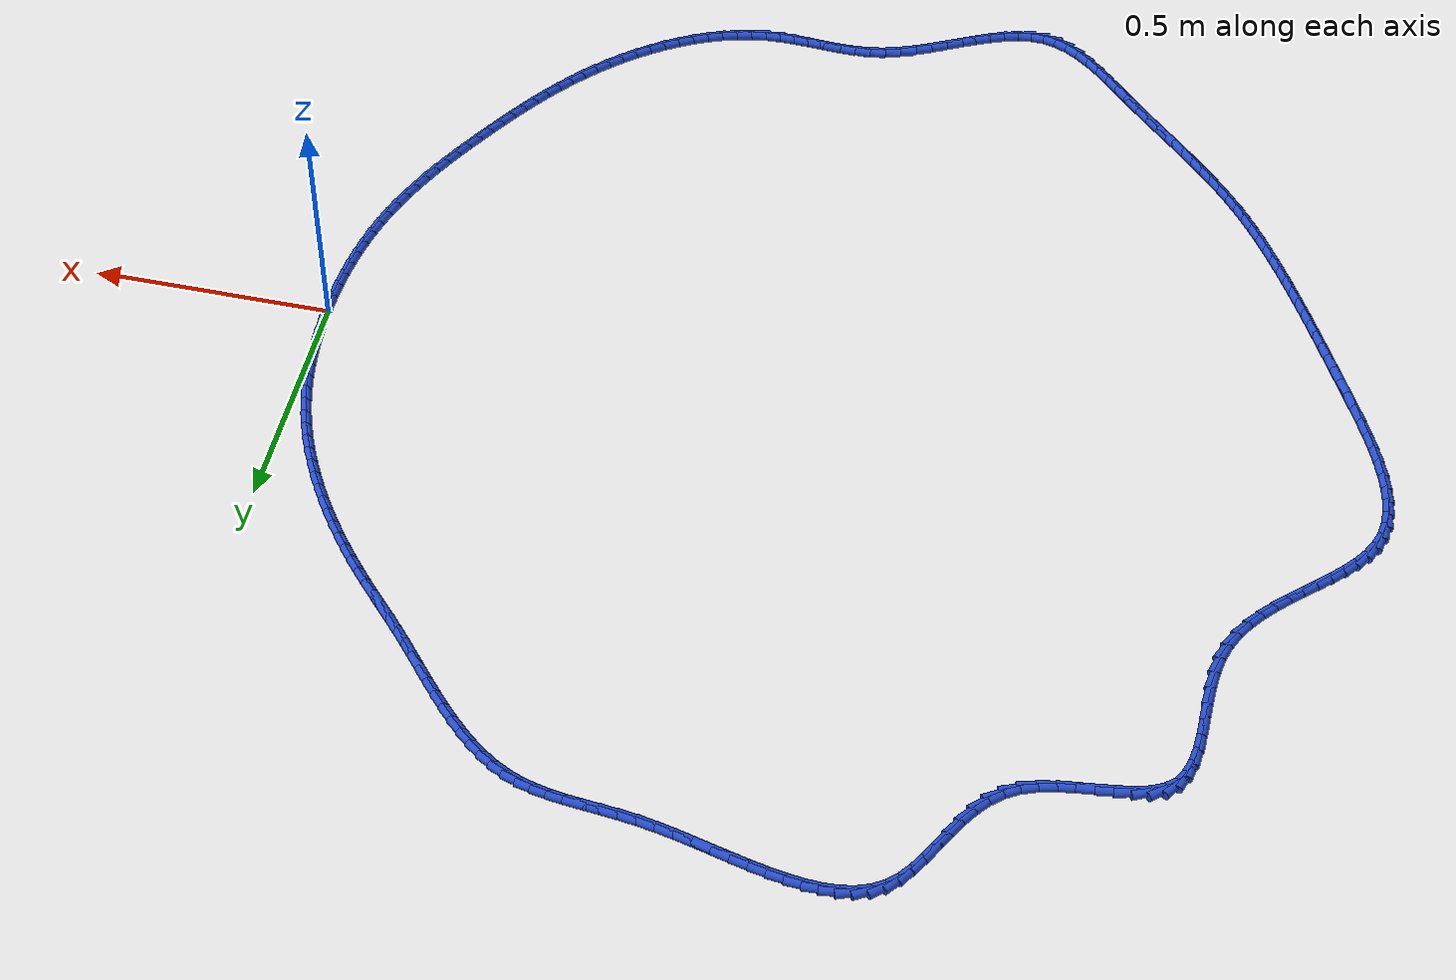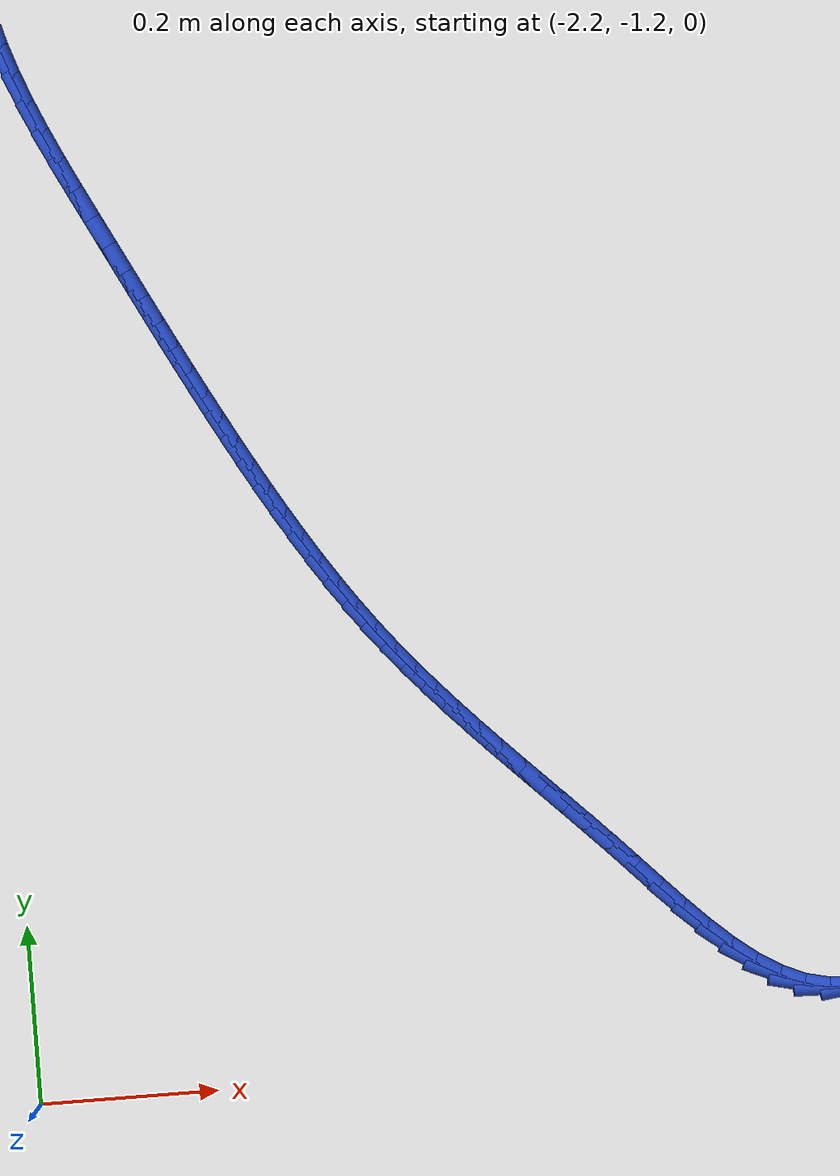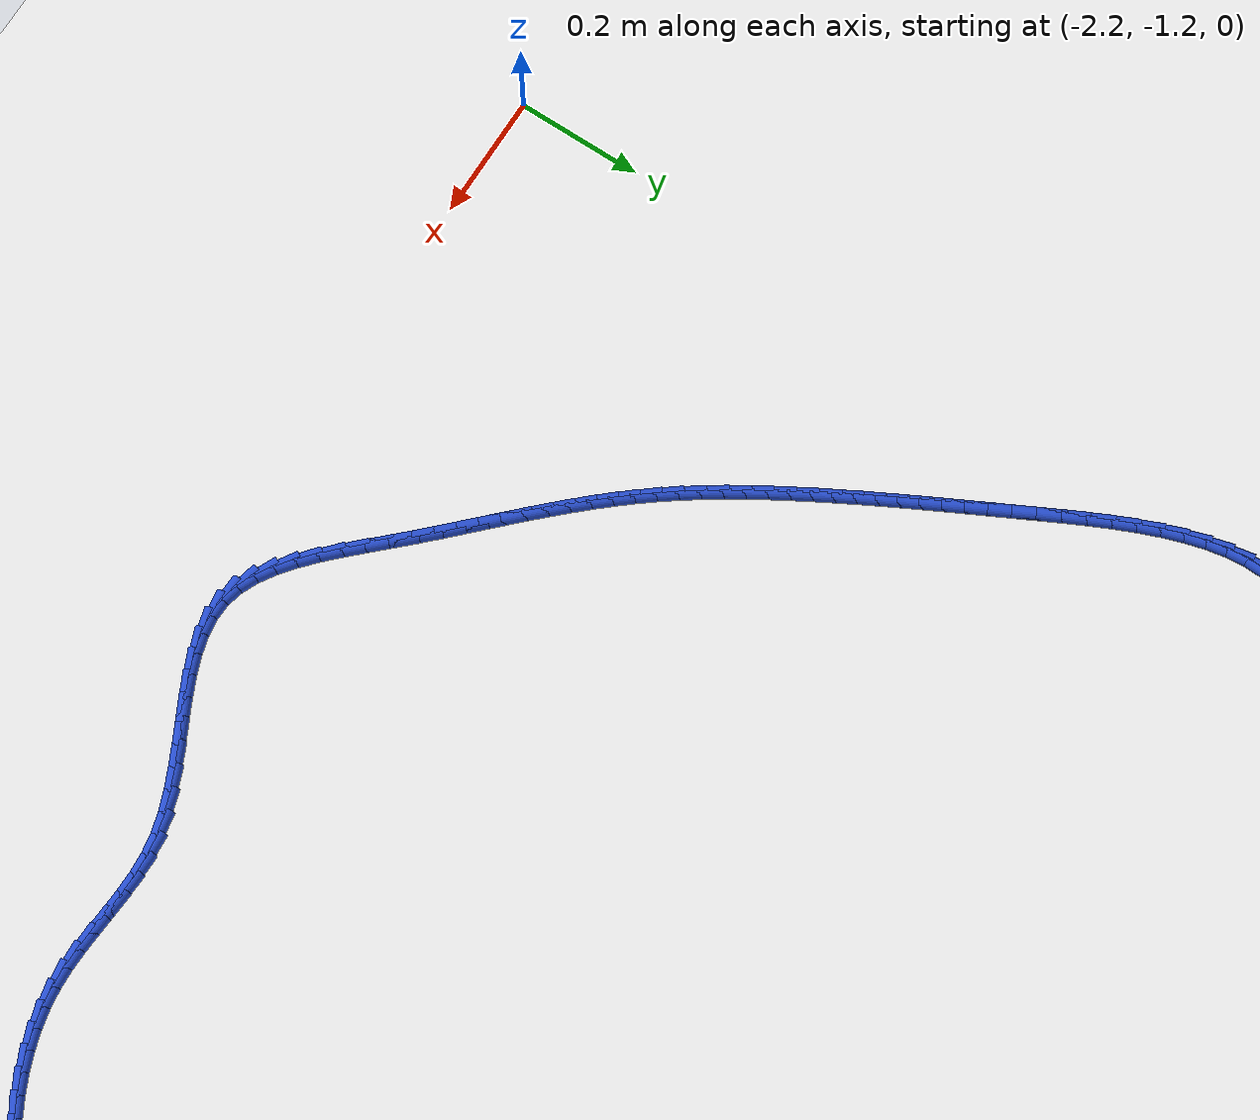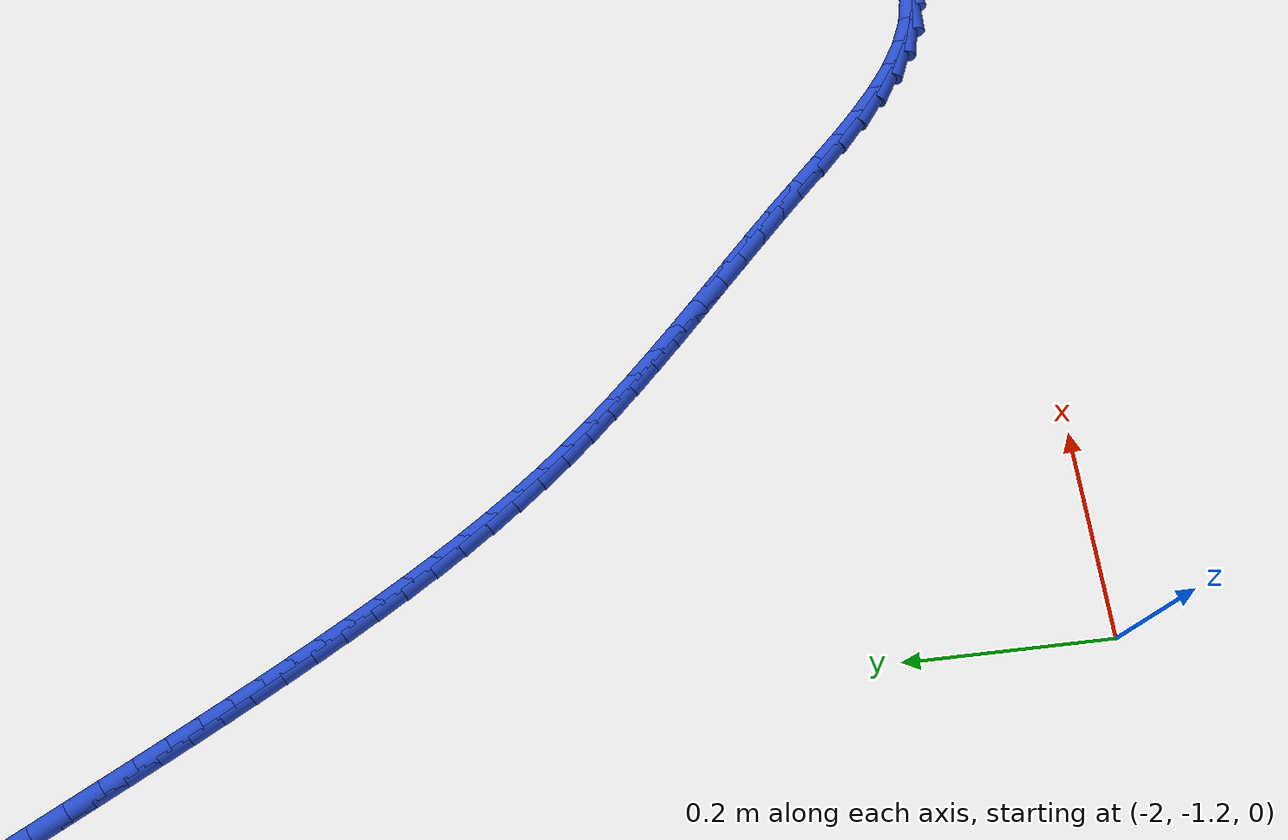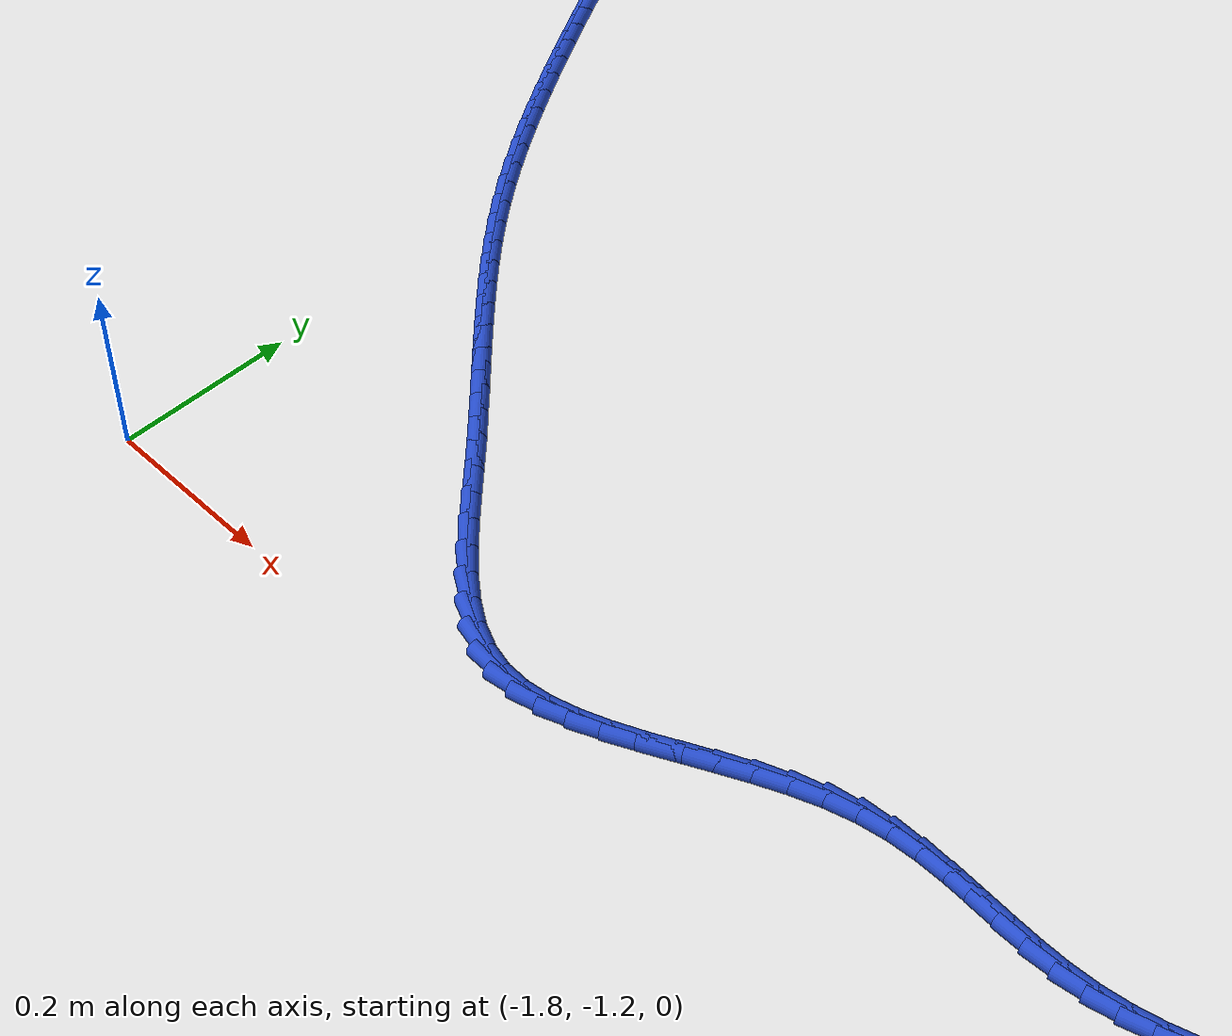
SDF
<sdf version="1.6">
 <world name="default">
  <light name="sun" type="directional">
   <pose>0 0 10 0 -0 0</pose>
   <diffuse>0.8 0.8 0.8 1</diffuse>
   <specular>0.2 0.2 0.2 1</specular>
   <attenuation>
    <range>1000</range>
    <constant>0.9</constant>
    <linear>0.01</linear>
    <quadratic>0.001</quadratic>
   </attenuation>
   <direction>-0.5 0.1 -0.9</direction>
  </light>
  <model name="ground_plane">
   <static>1</static>
   <link name="link">
    <collision name="collision">
     <geometry><plane><normal>0 0 1</normal><size>100 100</size></plane></geometry>
     <surface><friction><ode><mu>100</mu><mu2>50</mu2></ode></friction></surface>
    </collision>
    <visual name="visual">
     <cast_shadows>0</cast_shadows>
     <geometry><plane><normal>0 0 1</normal><size>100 100</size></plane></geometry>
     <material>
      <script><uri>file://media/materials/scripts/gazebo.material</uri><name>Gazebo/WhiteGlow</name></script>
     </material>
    </visual>
   </link>
  </model>
  <gravity>0 0 -9.8</gravity>
  <magnetic_field>6e-06 2.3e-05 -4.2e-05</magnetic_field>
  <atmosphere type="adiabatic"/>
  <physics name="default_physics" default="0" type="ode">
   <max_step_size>0.001</max_step_size>
   <real_time_factor>1</real_time_factor>
   <real_time_update_rate>1000</real_time_update_rate>
  </physics>
  <scene><ambient>0.4 0.4 0.4 1</ambient><background>0.7 0.7 0.7 1</background><shadows>1</shadows></scene>
  <spherical_coordinates>
   <surface_model>EARTH_WGS84</surface_model>
   <latitude_deg>0</latitude_deg>
   <longitude_deg>0</longitude_deg>
   <elevation>0</elevation>
   <heading_deg>0</heading_deg>
  </spherical_coordinates>
  <model name="line">
   <link name="link_0">
    <pose>-5.204170427930421e-18 -9.020562075079397e-17 0.01 0 1.57 -1.5581858213434019</pose>
    <collision name="collision">
     <geometry><cylinder><radius>0.01</radius><length>0.08</length></cylinder></geometry>
    </collision>
    <visual name="visual">
     <material>
      <script><name>Gazebo/Blue</name><uri>file://media/materials/scripts/gazebo.material</uri></script>
     </material>
     <geometry><cylinder><radius>0.01</radius><length>0.08</length></cylinder></geometry>
    </visual>
   </link>
   <link name="link_1">
    <pose>-0.00041625024051693304 0.03300646252234803 0.01 0 1.57 -1.5276875130593688</pose>
    <collision name="collision">
     <geometry><cylinder><radius>0.01</radius><length>0.08</length></cylinder></geometry>
    </collision>
    <visual name="visual">
     <material>
      <script><name>Gazebo/Blue</name><uri>file://media/materials/scripts/gazebo.material</uri></script>
     </material>
     <geometry><cylinder><radius>0.01</radius><length>0.08</length></cylinder></geometry>
    </visual>
   </link>
   <link name="link_2">
    <pose>-0.0018379684515828368 0.06596578768294657 0.01 0 1.57 -1.495853896881133</pose>
    <collision name="collision">
     <geometry><cylinder><radius>0.01</radius><length>0.08</length></cylinder></geometry>
    </collision>
    <visual name="visual">
     <material>
      <script><name>Gazebo/Blue</name><uri>file://media/materials/scripts/gazebo.material</uri></script>
     </material>
     <geometry><cylinder><radius>0.01</radius><length>0.08</length></cylinder></geometry>
    </visual>
   </link>
   <link name="link_3">
    <pose>-0.004305659109008439 0.09883193720745101 0.01 0 1.57 -1.4626195965446775</pose>
    <collision name="collision">
     <geometry><cylinder><radius>0.01</radius><length>0.08</length></cylinder></geometry>
    </collision>
    <visual name="visual">
     <material>
      <script><name>Gazebo/Blue</name><uri>file://media/materials/scripts/gazebo.material</uri></script>
     </material>
     <geometry><cylinder><radius>0.01</radius><length>0.08</length></cylinder></geometry>
    </visual>
   </link>
   <link name="link_4">
    <pose>-0.007859826688604462 0.13155887282151715 0.01 0 1.57 -1.4279255702663163</pose>
    <collision name="collision">
     <geometry><cylinder><radius>0.01</radius><length>0.08</length></cylinder></geometry>
    </collision>
    <visual name="visual">
     <material>
      <script><name>Gazebo/Blue</name><uri>file://media/materials/scripts/gazebo.material</uri></script>
     </material>
     <geometry><cylinder><radius>0.01</radius><length>0.08</length></cylinder></geometry>
    </visual>
   </link>
   <link name="link_5">
    <pose>-0.012540975666181616 0.16410055625080058 0.01 0 1.57 -1.3917213437353402</pose>
    <collision name="collision">
     <geometry><cylinder><radius>0.01</radius><length>0.08</length></cylinder></geometry>
    </collision>
    <visual name="visual">
     <material>
      <script><name>Gazebo/Blue</name><uri>file://media/materials/scripts/gazebo.material</uri></script>
     </material>
     <geometry><cylinder><radius>0.01</radius><length>0.08</length></cylinder></geometry>
    </visual>
   </link>
   <link name="link_6">
    <pose>-0.018389610517550635 0.196410949220957 0.01 0 1.57 -1.353967596230536</pose>
    <collision name="collision">
     <geometry><cylinder><radius>0.01</radius><length>0.08</length></cylinder></geometry>
    </collision>
    <visual name="visual">
     <material>
      <script><name>Gazebo/Blue</name><uri>file://media/materials/scripts/gazebo.material</uri></script>
     </material>
     <geometry><cylinder><radius>0.01</radius><length>0.08</length></cylinder></geometry>
    </visual>
   </link>
   <link name="link_7">
    <pose>-0.025446235718522225 0.22844401345764204 0.01 0 1.57 -1.3146390618482513</pose>
    <collision name="collision">
     <geometry><cylinder><radius>0.01</radius><length>0.08</length></cylinder></geometry>
    </collision>
    <visual name="visual">
     <material>
      <script><name>Gazebo/Blue</name><uri>file://media/materials/scripts/gazebo.material</uri></script>
     </material>
     <geometry><cylinder><radius>0.01</radius><length>0.08</length></cylinder></geometry>
    </visual>
   </link>
   <link name="link_8">
    <pose>-0.0337513557449071 0.2601537106865113 0.01 0 1.57 -1.2737276682083056</pose>
    <collision name="collision">
     <geometry><cylinder><radius>0.01</radius><length>0.08</length></cylinder></geometry>
    </collision>
    <visual name="visual">
     <material>
      <script><name>Gazebo/Blue</name><uri>file://media/materials/scripts/gazebo.material</uri></script>
     </material>
     <geometry><cylinder><radius>0.01</radius><length>0.08</length></cylinder></geometry>
    </visual>
   </link>
   <link name="link_9">
    <pose>-0.043345475072515974 0.29149400263322034 0.01 0 1.57 -1.2316776889360885</pose>
    <collision name="collision">
     <geometry><cylinder><radius>0.01</radius><length>0.08</length></cylinder></geometry>
    </collision>
    <visual name="visual">
     <material>
      <script><name>Gazebo/Blue</name><uri>file://media/materials/scripts/gazebo.material</uri></script>
     </material>
     <geometry><cylinder><radius>0.01</radius><length>0.08</length></cylinder></geometry>
    </visual>
   </link>
   <link name="link_10">
    <pose>-0.054255466085487127 0.3224227877599737 0.01 0 1.57 -1.1908780590909505</pose>
    <collision name="collision">
     <geometry><cylinder><radius>0.01</radius><length>0.08</length></cylinder></geometry>
    </collision>
    <visual name="visual">
     <material>
      <script><name>Gazebo/Blue</name><uri>file://media/materials/scripts/gazebo.material</uri></script>
     </material>
     <geometry><cylinder><radius>0.01</radius><length>0.08</length></cylinder></geometry>
    </visual>
   </link>
   <link name="link_11">
    <pose>-0.06643337950137554 0.3529195718652918 0.01 0 1.57 -1.1521259638891292</pose>
    <collision name="collision">
     <geometry><cylinder><radius>0.01</radius><length>0.08</length></cylinder></geometry>
    </collision>
    <visual name="visual">
     <material>
      <script><name>Gazebo/Blue</name><uri>file://media/materials/scripts/gazebo.material</uri></script>
     </material>
     <geometry><cylinder><radius>0.01</radius><length>0.08</length></cylinder></geometry>
    </visual>
   </link>
   <link name="link_12">
    <pose>-0.0798057293247777 0.3829712353541494 0.01 0 1.57 -1.1153851185606396</pose>
    <collision name="collision">
     <geometry><cylinder><radius>0.01</radius><length>0.08</length></cylinder></geometry>
    </collision>
    <visual name="visual">
     <material>
      <script><name>Gazebo/Blue</name><uri>file://media/materials/scripts/gazebo.material</uri></script>
     </material>
     <geometry><cylinder><radius>0.01</radius><length>0.08</length></cylinder></geometry>
    </visual>
   </link>
   <link name="link_13">
    <pose>-0.09429900768920726 0.412564664947551 0.01 0 1.57 -1.0806005177791245</pose>
    <collision name="collision">
     <geometry><cylinder><radius>0.01</radius><length>0.08</length></cylinder></geometry>
    </collision>
    <visual name="visual">
     <material>
      <script><name>Gazebo/Blue</name><uri>file://media/materials/scripts/gazebo.material</uri></script>
     </material>
     <geometry><cylinder><radius>0.01</radius><length>0.08</length></cylinder></geometry>
    </visual>
   </link>
   <link name="link_14">
    <pose>-0.10983970672817783 0.44168674736650076 0.01 0 1.57 -1.0477038576816564</pose>
    <collision name="collision">
     <geometry><cylinder><radius>0.01</radius><length>0.08</length></cylinder></geometry>
    </collision>
    <visual name="visual">
     <material>
      <script><name>Gazebo/Blue</name><uri>file://media/materials/scripts/gazebo.material</uri></script>
     </material>
     <geometry><cylinder><radius>0.01</radius><length>0.08</length></cylinder></geometry>
    </visual>
   </link>
   <link name="link_15">
    <pose>-0.1263543185752029 0.47032436933200306 0.01 0 1.57 -1.016617632504621</pose>
    <collision name="collision">
     <geometry><cylinder><radius>0.01</radius><length>0.08</length></cylinder></geometry>
    </collision>
    <visual name="visual">
     <material>
      <script><name>Gazebo/Blue</name><uri>file://media/materials/scripts/gazebo.material</uri></script>
     </material>
     <geometry><cylinder><radius>0.01</radius><length>0.08</length></cylinder></geometry>
    </visual>
   </link>
   <link name="link_16">
    <pose>-0.14376933536379616 0.49846441756506205 0.01 0 1.57 -0.9872585701645155</pose>
    <collision name="collision">
     <geometry><cylinder><radius>0.01</radius><length>0.08</length></cylinder></geometry>
    </collision>
    <visual name="visual">
     <material>
      <script><name>Gazebo/Blue</name><uri>file://media/materials/scripts/gazebo.material</uri></script>
     </material>
     <geometry><cylinder><radius>0.01</radius><length>0.08</length></cylinder></geometry>
    </visual>
   </link>
   <link name="link_17">
    <pose>-0.16201124922747104 0.5260937787866821 0.01 0 1.57 -0.9595404313695587</pose>
    <collision name="collision">
     <geometry><cylinder><radius>0.01</radius><length>0.08</length></cylinder></geometry>
    </collision>
    <visual name="visual">
     <material>
      <script><name>Gazebo/Blue</name><uri>file://media/materials/scripts/gazebo.material</uri></script>
     </material>
     <geometry><cylinder><radius>0.01</radius><length>0.08</length></cylinder></geometry>
    </visual>
   </link>
   <link name="link_18">
    <pose>-0.18100655229974133 0.5531993397178676 0.01 0 1.57 -0.9333762293121596</pose>
    <collision name="collision">
     <geometry><cylinder><radius>0.01</radius><length>0.08</length></cylinder></geometry>
    </collision>
    <visual name="visual">
     <material>
      <script><name>Gazebo/Blue</name><uri>file://media/materials/scripts/gazebo.material</uri></script>
     </material>
     <geometry><cylinder><radius>0.01</radius><length>0.08</length></cylinder></geometry>
    </visual>
   </link>
   <link name="link_19">
    <pose>-0.2006817367141205 0.5797679870796226 0.01 0 1.57 -0.908679943496282</pose>
    <collision name="collision">
     <geometry><cylinder><radius>0.01</radius><length>0.08</length></cylinder></geometry>
    </collision>
    <visual name="visual">
     <material>
      <script><name>Gazebo/Blue</name><uri>file://media/materials/scripts/gazebo.material</uri></script>
     </material>
     <geometry><cylinder><radius>0.01</radius><length>0.08</length></cylinder></geometry>
    </visual>
   </link>
   <link name="link_20">
    <pose>-0.2209632946041221 0.6057866075929514 0.01 0 1.57 -0.8853678064941394</pose>
    <collision name="collision">
     <geometry><cylinder><radius>0.01</radius><length>0.08</length></cylinder></geometry>
    </collision>
    <visual name="visual">
     <material>
      <script><name>Gazebo/Blue</name><uri>file://media/materials/scripts/gazebo.material</uri></script>
     </material>
     <geometry><cylinder><radius>0.01</radius><length>0.08</length></cylinder></geometry>
    </visual>
   </link>
   <link name="link_21">
    <pose>-0.2417777181032598 0.6312420879788588 0.01 0 1.57 -0.8633592404002483</pose>
    <collision name="collision">
     <geometry><cylinder><radius>0.01</radius><length>0.08</length></cylinder></geometry>
    </collision>
    <visual name="visual">
     <material>
      <script><name>Gazebo/Blue</name><uri>file://media/materials/scripts/gazebo.material</uri></script>
     </material>
     <geometry><cylinder><radius>0.01</radius><length>0.08</length></cylinder></geometry>
    </visual>
   </link>
   <link name="link_22">
    <pose>-0.2630514993450471 0.6561213149583486 0.01 0 1.57 -0.8429819206663465</pose>
    <collision name="collision">
     <geometry><cylinder><radius>0.01</radius><length>0.08</length></cylinder></geometry>
    </collision>
    <visual name="visual">
     <material>
      <script><name>Gazebo/Blue</name><uri>file://media/materials/scripts/gazebo.material</uri></script>
     </material>
     <geometry><cylinder><radius>0.01</radius><length>0.08</length></cylinder></geometry>
    </visual>
   </link>
   <link name="link_23">
    <pose>-0.2847099743242084 0.6804296617883872 0.01 0 1.57 -0.8281848112918715</pose>
    <collision name="collision">
     <geometry><cylinder><radius>0.01</radius><length>0.08</length></cylinder></geometry>
    </collision>
    <visual name="visual">
     <material>
      <script><name>Gazebo/Blue</name><uri>file://media/materials/scripts/gazebo.material</uri></script>
     </material>
     <geometry><cylinder><radius>0.01</radius><length>0.08</length></cylinder></geometry>
    </visual>
   </link>
   <link name="link_24">
    <pose>-0.3066673037927108 0.7043511926659936 0.01 0 1.57 -0.8213705310832886</pose>
    <collision name="collision">
     <geometry><cylinder><radius>0.01</radius><length>0.08</length></cylinder></geometry>
    </collision>
    <visual name="visual">
     <material>
      <script><name>Gazebo/Blue</name><uri>file://media/materials/scripts/gazebo.material</uri></script>
     </material>
     <geometry><cylinder><radius>0.01</radius><length>0.08</length></cylinder></geometry>
    </visual>
   </link>
   <link name="link_25">
    <pose>-0.3288313861517711 0.7281701061089301 0.01 0 1.57 -0.8226092343197998</pose>
    <collision name="collision">
     <geometry><cylinder><radius>0.01</radius><length>0.08</length></cylinder></geometry>
    </collision>
    <visual name="visual">
     <material>
      <script><name>Gazebo/Blue</name><uri>file://media/materials/scripts/gazebo.material</uri></script>
     </material>
     <geometry><cylinder><radius>0.01</radius><length>0.08</length></cylinder></geometry>
    </visual>
   </link>
   <link name="link_26">
    <pose>-0.35111005078721735 0.7521717041836616 0.01 0 1.57 -0.8317297002062111</pose>
    <collision name="collision">
     <geometry><cylinder><radius>0.01</radius><length>0.08</length></cylinder></geometry>
    </collision>
    <visual name="visual">
     <material>
      <script><name>Gazebo/Blue</name><uri>file://media/materials/scripts/gazebo.material</uri></script>
     </material>
     <geometry><cylinder><radius>0.01</radius><length>0.08</length></cylinder></geometry>
    </visual>
   </link>
   <link name="link_27">
    <pose>-0.37341112708487795 0.7766412889566531 0.01 0 1.57 -0.847632205602835</pose>
    <collision name="collision">
     <geometry><cylinder><radius>0.01</radius><length>0.08</length></cylinder></geometry>
    </collision>
    <visual name="visual">
     <material>
      <script><name>Gazebo/Blue</name><uri>file://media/materials/scripts/gazebo.material</uri></script>
     </material>
     <geometry><cylinder><radius>0.01</radius><length>0.08</length></cylinder></geometry>
    </visual>
   </link>
   <link name="link_28">
    <pose>-0.3956509368412511 0.8018370214054659 0.01 0 1.57 -0.8609041498238644</pose>
    <collision name="collision">
     <geometry><cylinder><radius>0.01</radius><length>0.08</length></cylinder></geometry>
    </collision>
    <visual name="visual">
     <material>
      <script><name>Gazebo/Blue</name><uri>file://media/materials/scripts/gazebo.material</uri></script>
     </material>
     <geometry><cylinder><radius>0.01</radius><length>0.08</length></cylinder></geometry>
    </visual>
   </link>
   <link name="link_29">
    <pose>-0.4178532981766036 0.8276735125554032 0.01 0 1.57 -0.8656417425640428</pose>
    <collision name="collision">
     <geometry><cylinder><radius>0.01</radius><length>0.08</length></cylinder></geometry>
    </collision>
    <visual name="visual">
     <material>
      <script><name>Gazebo/Blue</name><uri>file://media/materials/scripts/gazebo.material</uri></script>
     </material>
     <geometry><cylinder><radius>0.01</radius><length>0.08</length></cylinder></geometry>
    </visual>
   </link>
   <link name="link_30">
    <pose>-0.4401157878347854 0.8538296465648259 0.01 0 1.57 -0.8620089077731679</pose>
    <collision name="collision">
     <geometry><cylinder><radius>0.01</radius><length>0.08</length></cylinder></geometry>
    </collision>
    <visual name="visual">
     <material>
      <script><name>Gazebo/Blue</name><uri>file://media/materials/scripts/gazebo.material</uri></script>
     </material>
     <geometry><cylinder><radius>0.01</radius><length>0.08</length></cylinder></geometry>
    </visual>
   </link>
   <link name="link_31">
    <pose>-0.4625374258976617 0.8799796947952138 0.01 0 1.57 -0.8500205127177866</pose>
    <collision name="collision">
     <geometry><cylinder><radius>0.01</radius><length>0.08</length></cylinder></geometry>
    </collision>
    <visual name="visual">
     <material>
      <script><name>Gazebo/Blue</name><uri>file://media/materials/scripts/gazebo.material</uri></script>
     </material>
     <geometry><cylinder><radius>0.01</radius><length>0.08</length></cylinder></geometry>
    </visual>
   </link>
   <link name="link_32">
    <pose>-0.4852172324470993 0.905797928608048 0.01 0 1.57 -0.8294318722910394</pose>
    <collision name="collision">
     <geometry><cylinder><radius>0.01</radius><length>0.08</length></cylinder></geometry>
    </collision>
    <visual name="visual">
     <material>
      <script><name>Gazebo/Blue</name><uri>file://media/materials/scripts/gazebo.material</uri></script>
     </material>
     <geometry><cylinder><radius>0.01</radius><length>0.08</length></cylinder></geometry>
    </visual>
   </link>
   <link name="link_33">
    <pose>-0.5082542275649639 0.9309586193648087 0.01 0 1.57 -0.7997501536717067</pose>
    <collision name="collision">
     <geometry><cylinder><radius>0.01</radius><length>0.08</length></cylinder></geometry>
    </collision>
    <visual name="visual">
     <material>
      <script><name>Gazebo/Blue</name><uri>file://media/materials/scripts/gazebo.material</uri></script>
     </material>
     <geometry><cylinder><radius>0.01</radius><length>0.08</length></cylinder></geometry>
    </visual>
   </link>
   <link name="link_34">
    <pose>-0.5317474313331215 0.9551360384269767 0.01 0 1.57 -0.7602522932787537</pose>
    <collision name="collision">
     <geometry><cylinder><radius>0.01</radius><length>0.08</length></cylinder></geometry>
    </collision>
    <visual name="visual">
     <material>
      <script><name>Gazebo/Blue</name><uri>file://media/materials/scripts/gazebo.material</uri></script>
     </material>
     <geometry><cylinder><radius>0.01</radius><length>0.08</length></cylinder></geometry>
    </visual>
   </link>
   <link name="link_35">
    <pose>-0.5557958638334384 0.9780044571560323 0.01 0 1.57 -0.7100239108926873</pose>
    <collision name="collision">
     <geometry><cylinder><radius>0.01</radius><length>0.08</length></cylinder></geometry>
    </collision>
    <visual name="visual">
     <material>
      <script><name>Gazebo/Blue</name><uri>file://media/materials/scripts/gazebo.material</uri></script>
     </material>
     <geometry><cylinder><radius>0.01</radius><length>0.08</length></cylinder></geometry>
    </visual>
   </link>
   <link name="link_36">
    <pose>-0.5804985451477803 0.9992381469134562 0.01 0 1.57 -0.6480429347056867</pose>
    <collision name="collision">
     <geometry><cylinder><radius>0.01</radius><length>0.08</length></cylinder></geometry>
    </collision>
    <visual name="visual">
     <material>
      <script><name>Gazebo/Blue</name><uri>file://media/materials/scripts/gazebo.material</uri></script>
     </material>
     <geometry><cylinder><radius>0.01</radius><length>0.08</length></cylinder></geometry>
    </visual>
   </link>
   <link name="link_37">
    <pose>-0.605954495358014 1.0185113790607296 0.01 0 1.57 -0.5733414916751446</pose>
    <collision name="collision">
     <geometry><cylinder><radius>0.01</radius><length>0.08</length></cylinder></geometry>
    </collision>
    <visual name="visual">
     <material>
      <script><name>Gazebo/Blue</name><uri>file://media/materials/scripts/gazebo.material</uri></script>
     </material>
     <geometry><cylinder><radius>0.01</radius><length>0.08</length></cylinder></geometry>
    </visual>
   </link>
   <link name="link_38">
    <pose>-0.6322627345460051 1.0354984249593322 0.01 0 1.57 -0.4852819497625088</pose>
    <collision name="collision">
     <geometry><cylinder><radius>0.01</radius><length>0.08</length></cylinder></geometry>
    </collision>
    <visual name="visual">
     <material>
      <script><name>Gazebo/Blue</name><uri>file://media/materials/scripts/gazebo.material</uri></script>
     </material>
     <geometry><cylinder><radius>0.01</radius><length>0.08</length></cylinder></geometry>
    </visual>
   </link>
   <link name="link_39">
    <pose>-0.6595222827936195 1.0498735559707448 0.01 0 1.57 -0.38421383837616646</pose>
    <collision name="collision">
     <geometry><cylinder><radius>0.01</radius><length>0.08</length></cylinder></geometry>
    </collision>
    <visual name="visual">
     <material>
      <script><name>Gazebo/Blue</name><uri>file://media/materials/scripts/gazebo.material</uri></script>
     </material>
     <geometry><cylinder><radius>0.01</radius><length>0.08</length></cylinder></geometry>
    </visual>
   </link>
   <link name="link_40">
    <pose>-0.687830992698426 1.0613189673043768 0.01 0 1.57 -0.2839456350210226</pose>
    <collision name="collision">
     <geometry><cylinder><radius>0.01</radius><length>0.08</length></cylinder></geometry>
    </collision>
    <visual name="visual">
     <material>
      <script><name>Gazebo/Blue</name><uri>file://media/materials/scripts/gazebo.material</uri></script>
     </material>
     <geometry><cylinder><radius>0.01</radius><length>0.08</length></cylinder></geometry>
    </visual>
   </link>
   <link name="link_41">
    <pose>-0.7172304642286119 1.069898647125397 0.01 0 1.57 -0.20467913233329538</pose>
    <collision name="collision">
     <geometry><cylinder><radius>0.01</radius><length>0.08</length></cylinder></geometry>
    </collision>
    <visual name="visual">
     <material>
      <script><name>Gazebo/Blue</name><uri>file://media/materials/scripts/gazebo.material</uri></script>
     </material>
     <geometry><cylinder><radius>0.01</radius><length>0.08</length></cylinder></geometry>
    </visual>
   </link>
   <link name="link_42">
    <pose>-0.7476822299060225 1.076220010410051 0.01 0 1.57 -0.14867417123021967</pose>
    <collision name="collision">
     <geometry><cylinder><radius>0.01</radius><length>0.08</length></cylinder></geometry>
    </collision>
    <visual name="visual">
     <material>
      <script><name>Gazebo/Blue</name><uri>file://media/materials/scripts/gazebo.material</uri></script>
     </material>
     <geometry><cylinder><radius>0.01</radius><length>0.08</length></cylinder></geometry>
    </visual>
   </link>
   <link name="link_43">
    <pose>-0.7791417049519479 1.0809319909450978 0.01 0 1.57 -0.11519504199792617</pose>
    <collision name="collision">
     <geometry><cylinder><radius>0.01</radius><length>0.08</length></cylinder></geometry>
    </collision>
    <visual name="visual">
     <material>
      <script><name>Gazebo/Blue</name><uri>file://media/materials/scripts/gazebo.material</uri></script>
     </material>
     <geometry><cylinder><radius>0.01</radius><length>0.08</length></cylinder></geometry>
    </visual>
   </link>
   <link name="link_44">
    <pose>-0.8115643045876787 1.0846835225172988 0.01 0 1.57 -0.10281253430681717</pose>
    <collision name="collision">
     <geometry><cylinder><radius>0.01</radius><length>0.08</length></cylinder></geometry>
    </collision>
    <visual name="visual">
     <material>
      <script><name>Gazebo/Blue</name><uri>file://media/materials/scripts/gazebo.material</uri></script>
     </material>
     <geometry><cylinder><radius>0.01</radius><length>0.08</length></cylinder></geometry>
    </visual>
   </link>
   <link name="link_45">
    <pose>-0.8449054440345043 1.088123538913414 0.01 0 1.57 -0.10995728506994472</pose>
    <collision name="collision">
     <geometry><cylinder><radius>0.01</radius><length>0.08</length></cylinder></geometry>
    </collision>
    <visual name="visual">
     <material>
      <script><name>Gazebo/Blue</name><uri>file://media/materials/scripts/gazebo.material</uri></script>
     </material>
     <geometry><cylinder><radius>0.01</radius><length>0.08</length></cylinder></geometry>
    </visual>
   </link>
   <link name="link_46">
    <pose>-0.8791205385137147 1.0919009739202035 0.01 0 1.57 -0.13510738535948888</pose>
    <collision name="collision">
     <geometry><cylinder><radius>0.01</radius><length>0.08</length></cylinder></geometry>
    </collision>
    <visual name="visual">
     <material>
      <script><name>Gazebo/Blue</name><uri>file://media/materials/scripts/gazebo.material</uri></script>
     </material>
     <geometry><cylinder><radius>0.01</radius><length>0.08</length></cylinder></geometry>
    </visual>
   </link>
   <link name="link_47">
    <pose>-0.9141650032466005 1.0966647613244282 0.01 0 1.57 -0.17525803667830525</pose>
    <collision name="collision">
     <geometry><cylinder><radius>0.01</radius><length>0.08</length></cylinder></geometry>
    </collision>
    <visual name="visual">
     <material>
      <script><name>Gazebo/Blue</name><uri>file://media/materials/scripts/gazebo.material</uri></script>
     </material>
     <geometry><cylinder><radius>0.01</radius><length>0.08</length></cylinder></geometry>
    </visual>
   </link>
   <link name="link_48">
    <pose>-0.9499839964409275 1.1030073999631802 0.01 0 1.57 -0.2122378254546874</pose>
    <collision name="collision">
     <geometry><cylinder><radius>0.01</radius><length>0.08</length></cylinder></geometry>
    </collision>
    <visual name="visual">
     <material>
      <script><name>Gazebo/Blue</name><uri>file://media/materials/scripts/gazebo.material</uri></script>
     </material>
     <geometry><cylinder><radius>0.01</radius><length>0.08</length></cylinder></geometry>
    </visual>
   </link>
   <link name="link_49">
    <pose>-0.9864015167166088 1.1108547584476753 0.01 0 1.57 -0.23606342272071446</pose>
    <collision name="collision">
     <geometry><cylinder><radius>0.01</radius><length>0.08</length></cylinder></geometry>
    </collision>
    <visual name="visual">
     <material>
      <script><name>Gazebo/Blue</name><uri>file://media/materials/scripts/gazebo.material</uri></script>
     </material>
     <geometry><cylinder><radius>0.01</radius><length>0.08</length></cylinder></geometry>
    </visual>
   </link>
   <link name="link_50">
    <pose>-1.0231624728860538 1.1196975466272503 0.01 0 1.57 -0.24777251034618017</pose>
    <collision name="collision">
     <geometry><cylinder><radius>0.01</radius><length>0.08</length></cylinder></geometry>
    </collision>
    <visual name="visual">
     <material>
      <script><name>Gazebo/Blue</name><uri>file://media/materials/scripts/gazebo.material</uri></script>
     </material>
     <geometry><cylinder><radius>0.01</radius><length>0.08</length></cylinder></geometry>
    </visual>
   </link>
   <link name="link_51">
    <pose>-1.06001041353372 1.129018990262824 0.01 0 1.57 -0.24789425618512728</pose>
    <collision name="collision">
     <geometry><cylinder><radius>0.01</radius><length>0.08</length></cylinder></geometry>
    </collision>
    <visual name="visual">
     <material>
      <script><name>Gazebo/Blue</name><uri>file://media/materials/scripts/gazebo.material</uri></script>
     </material>
     <geometry><cylinder><radius>0.01</radius><length>0.08</length></cylinder></geometry>
    </visual>
   </link>
   <link name="link_52">
    <pose>-1.096688887244063 1.138302315115316 0.01 0 1.57 -0.23627041594963016</pose>
    <collision name="collision">
     <geometry><cylinder><radius>0.01</radius><length>0.08</length></cylinder></geometry>
    </collision>
    <visual name="visual">
     <material>
      <script><name>Gazebo/Blue</name><uri>file://media/materials/scripts/gazebo.material</uri></script>
     </material>
     <geometry><cylinder><radius>0.01</radius><length>0.08</length></cylinder></geometry>
    </visual>
   </link>
   <link name="link_53">
    <pose>-1.1329414426015403 1.1470307469456456 0.01 0 1.57 -0.21202268224467472</pose>
    <collision name="collision">
     <geometry><cylinder><radius>0.01</radius><length>0.08</length></cylinder></geometry>
    </collision>
    <visual name="visual">
     <material>
      <script><name>Gazebo/Blue</name><uri>file://media/materials/scripts/gazebo.material</uri></script>
     </material>
     <geometry><cylinder><radius>0.01</radius><length>0.08</length></cylinder></geometry>
    </visual>
   </link>
   <link name="link_54">
    <pose>-1.1685116281906063 1.1546875115147306 0.01 0 1.57 -0.17346515563223877</pose>
    <collision name="collision">
     <geometry><cylinder><radius>0.01</radius><length>0.08</length></cylinder></geometry>
    </collision>
    <visual name="visual">
     <material>
      <script><name>Gazebo/Blue</name><uri>file://media/materials/scripts/gazebo.material</uri></script>
     </material>
     <geometry><cylinder><radius>0.01</radius><length>0.08</length></cylinder></geometry>
    </visual>
   </link>
   <link name="link_55">
    <pose>-1.2031429925957187 1.1607558345834916 0.01 0 1.57 -0.11797740032045509</pose>
    <collision name="collision">
     <geometry><cylinder><radius>0.01</radius><length>0.08</length></cylinder></geometry>
    </collision>
    <visual name="visual">
     <material>
      <script><name>Gazebo/Blue</name><uri>file://media/materials/scripts/gazebo.material</uri></script>
     </material>
     <geometry><cylinder><radius>0.01</radius><length>0.08</length></cylinder></geometry>
    </visual>
   </link>
   <link name="link_56">
    <pose>-1.236579084401334 1.1647189419128468 0.01 0 1.57 -0.04190585294978433</pose>
    <collision name="collision">
     <geometry><cylinder><radius>0.01</radius><length>0.08</length></cylinder></geometry>
    </collision>
    <visual name="visual">
     <material>
      <script><name>Gazebo/Blue</name><uri>file://media/materials/scripts/gazebo.material</uri></script>
     </material>
     <geometry><cylinder><radius>0.01</radius><length>0.08</length></cylinder></geometry>
    </visual>
   </link>
   <link name="link_57">
    <pose>-1.2685634521919078 1.1660600592637156 0.01 0 1.57 0.05930530623426875</pose>
    <collision name="collision">
     <geometry><cylinder><radius>0.01</radius><length>0.08</length></cylinder></geometry>
    </collision>
    <visual name="visual">
     <material>
      <script><name>Gazebo/Blue</name><uri>file://media/materials/scripts/gazebo.material</uri></script>
     </material>
     <geometry><cylinder><radius>0.01</radius><length>0.08</length></cylinder></geometry>
    </visual>
   </link>
   <link name="link_58">
    <pose>-1.2988396445518964 1.1642624123970167 0.01 0 1.57 0.190283022876163</pose>
    <collision name="collision">
     <geometry><cylinder><radius>0.01</radius><length>0.08</length></cylinder></geometry>
    </collision>
    <visual name="visual">
     <material>
      <script><name>Gazebo/Blue</name><uri>file://media/materials/scripts/gazebo.material</uri></script>
     </material>
     <geometry><cylinder><radius>0.01</radius><length>0.08</length></cylinder></geometry>
    </visual>
   </link>
   <link name="link_59">
    <pose>-1.3271512100657574 1.1588092270736696 0.01 0 1.57 0.3534362279731515</pose>
    <collision name="collision">
     <geometry><cylinder><radius>0.01</radius><length>0.08</length></cylinder></geometry>
    </collision>
    <visual name="visual">
     <material>
      <script><name>Gazebo/Blue</name><uri>file://media/materials/scripts/gazebo.material</uri></script>
     </material>
     <geometry><cylinder><radius>0.01</radius><length>0.08</length></cylinder></geometry>
    </visual>
   </link>
   <link name="link_60">
    <pose>-1.3532416973179457 1.1491837290545932 0.01 0 1.57 0.5449785562453563</pose>
    <collision name="collision">
     <geometry><cylinder><radius>0.01</radius><length>0.08</length></cylinder></geometry>
    </collision>
    <visual name="visual">
     <material>
      <script><name>Gazebo/Blue</name><uri>file://media/materials/scripts/gazebo.material</uri></script>
     </material>
     <geometry><cylinder><radius>0.01</radius><length>0.08</length></cylinder></geometry>
    </visual>
   </link>
   <link name="link_61">
    <pose>-1.3768546548929186 1.1348691441007066 0.01 0 1.57 0.74917982172499</pose>
    <collision name="collision">
     <geometry><cylinder><radius>0.01</radius><length>0.08</length></cylinder></geometry>
    </collision>
    <visual name="visual">
     <material>
      <script><name>Gazebo/Blue</name><uri>file://media/materials/scripts/gazebo.material</uri></script>
     </material>
     <geometry><cylinder><radius>0.01</radius><length>0.08</length></cylinder></geometry>
    </visual>
   </link>
   <link name="link_62">
    <pose>-1.3977726674062538 1.1154140193786934 0.01 0 1.57 0.9142011144767906</pose>
    <collision name="collision">
     <geometry><cylinder><radius>0.01</radius><length>0.08</length></cylinder></geometry>
    </collision>
    <visual name="visual">
     <material>
      <script><name>Gazebo/Blue</name><uri>file://media/materials/scripts/gazebo.material</uri></script>
     </material>
     <geometry><cylinder><radius>0.01</radius><length>0.08</length></cylinder></geometry>
    </visual>
   </link>
   <link name="link_63">
    <pose>-1.4163449036745022 1.0913150024493528 0.01 0 1.57 1.0175417219230745</pose>
    <collision name="collision">
     <geometry><cylinder><radius>0.01</radius><length>0.08</length></cylinder></geometry>
    </collision>
    <visual name="visual">
     <material>
      <script><name>Gazebo/Blue</name><uri>file://media/materials/scripts/gazebo.material</uri></script>
     </material>
     <geometry><cylinder><radius>0.01</radius><length>0.08</length></cylinder></geometry>
    </visual>
   </link>
   <link name="link_64">
    <pose>-1.4333479044139852 1.0637838887119042 0.01 0 1.57 1.0713889321470484</pose>
    <collision name="collision">
     <geometry><cylinder><radius>0.01</radius><length>0.08</length></cylinder></geometry>
    </collision>
    <visual name="visual">
     <material>
      <script><name>Gazebo/Blue</name><uri>file://media/materials/scripts/gazebo.material</uri></script>
     </material>
     <geometry><cylinder><radius>0.01</radius><length>0.08</length></cylinder></geometry>
    </visual>
   </link>
   <link name="link_65">
    <pose>-1.4495687081223272 1.0340500401524442 0.01 0 1.57 1.0846889842860583</pose>
    <collision name="collision">
     <geometry><cylinder><radius>0.01</radius><length>0.08</length></cylinder></geometry>
    </collision>
    <visual name="visual">
     <material>
      <script><name>Gazebo/Blue</name><uri>file://media/materials/scripts/gazebo.material</uri></script>
     </material>
     <geometry><cylinder><radius>0.01</radius><length>0.08</length></cylinder></geometry>
    </visual>
   </link>
   <link name="link_66">
    <pose>-1.4657943532971525 1.0033428187570688 0.01 0 1.57 1.061187544373523</pose>
    <collision name="collision">
     <geometry><cylinder><radius>0.01</radius><length>0.08</length></cylinder></geometry>
    </collision>
    <visual name="visual">
     <material>
      <script><name>Gazebo/Blue</name><uri>file://media/materials/scripts/gazebo.material</uri></script>
     </material>
     <geometry><cylinder><radius>0.01</radius><length>0.08</length></cylinder></geometry>
    </visual>
   </link>
   <link name="link_67">
    <pose>-1.4828118784360846 0.972891586511875 0.01 0 1.57 1.0000570758252663</pose>
    <collision name="collision">
     <geometry><cylinder><radius>0.01</radius><length>0.08</length></cylinder></geometry>
    </collision>
    <visual name="visual">
     <material>
      <script><name>Gazebo/Blue</name><uri>file://media/materials/scripts/gazebo.material</uri></script>
     </material>
     <geometry><cylinder><radius>0.01</radius><length>0.08</length></cylinder></geometry>
    </visual>
   </link>
   <link name="link_68">
    <pose>-1.501408322036748 0.9439257054029591 0.01 0 1.57 0.896951080619771</pose>
    <collision name="collision">
     <geometry><cylinder><radius>0.01</radius><length>0.08</length></cylinder></geometry>
    </collision>
    <visual name="visual">
     <material>
      <script><name>Gazebo/Blue</name><uri>file://media/materials/scripts/gazebo.material</uri></script>
     </material>
     <geometry><cylinder><radius>0.01</radius><length>0.08</length></cylinder></geometry>
    </visual>
   </link>
   <link name="link_69">
    <pose>-1.5223707225967666 0.9176745374164174 0.01 0 1.57 0.7464646765375791</pose>
    <collision name="collision">
     <geometry><cylinder><radius>0.01</radius><length>0.08</length></cylinder></geometry>
    </collision>
    <visual name="visual">
     <material>
      <script><name>Gazebo/Blue</name><uri>file://media/materials/scripts/gazebo.material</uri></script>
     </material>
     <geometry><cylinder><radius>0.01</radius><length>0.08</length></cylinder></geometry>
    </visual>
   </link>
   <link name="link_70">
    <pose>-1.5464861186137648 0.8953674445383472 0.01 0 1.57 0.5500451787679549</pose>
    <collision name="collision">
     <geometry><cylinder><radius>0.01</radius><length>0.08</length></cylinder></geometry>
    </collision>
    <visual name="visual">
     <material>
      <script><name>Gazebo/Blue</name><uri>file://media/materials/scripts/gazebo.material</uri></script>
     </material>
     <geometry><cylinder><radius>0.01</radius><length>0.08</length></cylinder></geometry>
    </visual>
   </link>
   <link name="link_71">
    <pose>-1.5745050126741056 0.8781871727781128 0.01 0 1.57 0.3627292873530652</pose>
    <collision name="collision">
     <geometry><cylinder><radius>0.01</radius><length>0.08</length></cylinder></geometry>
    </collision>
    <visual name="visual">
     <material>
      <script><name>Gazebo/Blue</name><uri>file://media/materials/scripts/gazebo.material</uri></script>
     </material>
     <geometry><cylinder><radius>0.01</radius><length>0.08</length></cylinder></geometry>
    </visual>
   </link>
   <link name="link_72">
    <pose>-1.6062540440503577 0.8661377158092909 0.01 0 1.57 0.23322818545304894</pose>
    <collision name="collision">
     <geometry><cylinder><radius>0.01</radius><length>0.08</length></cylinder></geometry>
    </collision>
    <visual name="visual">
     <material>
      <script><name>Gazebo/Blue</name><uri>file://media/materials/scripts/gazebo.material</uri></script>
     </material>
     <geometry><cylinder><radius>0.01</radius><length>0.08</length></cylinder></geometry>
    </visual>
   </link>
   <link name="link_73">
    <pose>-1.6405870484406124 0.8579818723488492 0.01 0 1.57 0.15435716667984334</pose>
    <collision name="collision">
     <geometry><cylinder><radius>0.01</radius><length>0.08</length></cylinder></geometry>
    </collision>
    <visual name="visual">
     <material>
      <script><name>Gazebo/Blue</name><uri>file://media/materials/scripts/gazebo.material</uri></script>
     </material>
     <geometry><cylinder><radius>0.01</radius><length>0.08</length></cylinder></geometry>
    </visual>
   </link>
   <link name="link_74">
    <pose>-1.6763115294034057 0.8524233261809425 0.01 0 1.57 0.1179673883621963</pose>
    <collision name="collision">
     <geometry><cylinder><radius>0.01</radius><length>0.08</length></cylinder></geometry>
    </collision>
    <visual name="visual">
     <material>
      <script><name>Gazebo/Blue</name><uri>file://media/materials/scripts/gazebo.material</uri></script>
     </material>
     <geometry><cylinder><radius>0.01</radius><length>0.08</length></cylinder></geometry>
    </visual>
   </link>
   <link name="link_75">
    <pose>-1.712234990497275 0.8481657610897262 0.01 0 1.57 0.12115878743704452</pose>
    <collision name="collision">
     <geometry><cylinder><radius>0.01</radius><length>0.08</length></cylinder></geometry>
    </collision>
    <visual name="visual">
     <material>
      <script><name>Gazebo/Blue</name><uri>file://media/materials/scripts/gazebo.material</uri></script>
     </material>
     <geometry><cylinder><radius>0.01</radius><length>0.08</length></cylinder></geometry>
    </visual>
   </link>
   <link name="link_76">
    <pose>-1.7471649352807557 0.8439128608593549 0.01 0 1.57 0.16773954479128225</pose>
    <collision name="collision">
     <geometry><cylinder><radius>0.01</radius><length>0.08</length></cylinder></geometry>
    </collision>
    <visual name="visual">
     <material>
      <script><name>Gazebo/Blue</name><uri>file://media/materials/scripts/gazebo.material</uri></script>
     </material>
     <geometry><cylinder><radius>0.01</radius><length>0.08</length></cylinder></geometry>
    </visual>
   </link>
   <link name="link_77">
    <pose>-1.7799088673123835 0.8383683092739836 0.01 0 1.57 0.27017078201847866</pose>
    <collision name="collision">
     <geometry><cylinder><radius>0.01</radius><length>0.08</length></cylinder></geometry>
    </collision>
    <visual name="visual">
     <material>
      <script><name>Gazebo/Blue</name><uri>file://media/materials/scripts/gazebo.material</uri></script>
     </material>
     <geometry><cylinder><radius>0.01</radius><length>0.08</length></cylinder></geometry>
    </visual>
   </link>
   <link name="link_78">
    <pose>-1.809274290150696 0.8302357901177679 0.01 0 1.57 0.45129853389072266</pose>
    <collision name="collision">
     <geometry><cylinder><radius>0.01</radius><length>0.08</length></cylinder></geometry>
    </collision>
    <visual name="visual">
     <material>
      <script><name>Gazebo/Blue</name><uri>file://media/materials/scripts/gazebo.material</uri></script>
     </material>
     <geometry><cylinder><radius>0.01</radius><length>0.08</length></cylinder></geometry>
    </visual>
   </link>
   <link name="link_79">
    <pose>-1.8340687073542288 0.8182189871748619 0.01 0 1.57 0.7318105183051753</pose>
    <collision name="collision">
     <geometry><cylinder><radius>0.01</radius><length>0.08</length></cylinder></geometry>
    </collision>
    <visual name="visual">
     <material>
      <script><name>Gazebo/Blue</name><uri>file://media/materials/scripts/gazebo.material</uri></script>
     </material>
     <geometry><cylinder><radius>0.01</radius><length>0.08</length></cylinder></geometry>
    </visual>
   </link>
   <link name="link_80">
    <pose>-1.853156486820106 0.8010746615508723 0.01 0 1.57 1.0336173166899083</pose>
    <collision name="collision">
     <geometry><cylinder><radius>0.01</radius><length>0.08</length></cylinder></geometry>
    </collision>
    <visual name="visual">
     <material>
      <script><name>Gazebo/Blue</name><uri>file://media/materials/scripts/gazebo.material</uri></script>
     </material>
     <geometry><cylinder><radius>0.01</radius><length>0.08</length></cylinder></geometry>
    </visual>
   </link>
   <link name="link_81">
    <pose>-1.8665332196596895 0.7786154610400781 0.01 0 1.57 1.2588916427071157</pose>
    <collision name="collision">
     <geometry><cylinder><radius>0.01</radius><length>0.08</length></cylinder></geometry>
    </collision>
    <visual name="visual">
     <material>
      <script><name>Gazebo/Blue</name><uri>file://media/materials/scripts/gazebo.material</uri></script>
     </material>
     <geometry><cylinder><radius>0.01</radius><length>0.08</length></cylinder></geometry>
    </visual>
   </link>
   <link name="link_82">
    <pose>-1.8752354971380483 0.7516257056862028 0.01 0 1.57 1.4060735724981681</pose>
    <collision name="collision">
     <geometry><cylinder><radius>0.01</radius><length>0.08</length></cylinder></geometry>
    </collision>
    <visual name="visual">
     <material>
      <script><name>Gazebo/Blue</name><uri>file://media/materials/scripts/gazebo.material</uri></script>
     </material>
     <geometry><cylinder><radius>0.01</radius><length>0.08</length></cylinder></geometry>
    </visual>
   </link>
   <link name="link_83">
    <pose>-1.8803386911587163 0.720925913481723 0.01 0 1.57 1.4941520170989595</pose>
    <collision name="collision">
     <geometry><cylinder><radius>0.01</radius><length>0.08</length></cylinder></geometry>
    </collision>
    <visual name="visual">
     <material>
      <script><name>Gazebo/Blue</name><uri>file://media/materials/scripts/gazebo.material</uri></script>
     </material>
     <geometry><cylinder><radius>0.01</radius><length>0.08</length></cylinder></geometry>
    </visual>
   </link>
   <link name="link_84">
    <pose>-1.8829181736252292 0.6873366024191143 0.01 0 1.57 1.5390852453384432</pose>
    <collision name="collision">
     <geometry><cylinder><radius>0.01</radius><length>0.08</length></cylinder></geometry>
    </collision>
    <visual name="visual">
     <material>
      <script><name>Gazebo/Blue</name><uri>file://media/materials/scripts/gazebo.material</uri></script>
     </material>
     <geometry><cylinder><radius>0.01</radius><length>0.08</length></cylinder></geometry>
    </visual>
   </link>
   <link name="link_85">
    <pose>-1.8840493164411214 0.6516782904908526 0.01 0 1.57 1.5502562488359992</pose>
    <collision name="collision">
     <geometry><cylinder><radius>0.01</radius><length>0.08</length></cylinder></geometry>
    </collision>
    <visual name="visual">
     <material>
      <script><name>Gazebo/Blue</name><uri>file://media/materials/scripts/gazebo.material</uri></script>
     </material>
     <geometry><cylinder><radius>0.01</radius><length>0.08</length></cylinder></geometry>
    </visual>
   </link>
   <link name="link_86">
    <pose>-1.8848074915099287 0.6147714956894146 0.01 0 1.57 1.5316951031851787</pose>
    <collision name="collision">
     <geometry><cylinder><radius>0.01</radius><length>0.08</length></cylinder></geometry>
    </collision>
    <visual name="visual">
     <material>
      <script><name>Gazebo/Blue</name><uri>file://media/materials/scripts/gazebo.material</uri></script>
     </material>
     <geometry><cylinder><radius>0.01</radius><length>0.08</length></cylinder></geometry>
    </visual>
   </link>
   <link name="link_87">
    <pose>-1.886268070735185 0.5774367360072756 0.01 0 1.57 1.4833597925983442</pose>
    <collision name="collision">
     <geometry><cylinder><radius>0.01</radius><length>0.08</length></cylinder></geometry>
    </collision>
    <visual name="visual">
     <material>
      <script><name>Gazebo/Blue</name><uri>file://media/materials/scripts/gazebo.material</uri></script>
     </material>
     <geometry><cylinder><radius>0.01</radius><length>0.08</length></cylinder></geometry>
    </visual>
   </link>
   <link name="link_88">
    <pose>-1.8895064260204266 0.5404945294369118 0.01 0 1.57 1.4019288035196342</pose>
    <collision name="collision">
     <geometry><cylinder><radius>0.01</radius><length>0.08</length></cylinder></geometry>
    </collision>
    <visual name="visual">
     <material>
      <script><name>Gazebo/Blue</name><uri>file://media/materials/scripts/gazebo.material</uri></script>
     </material>
     <geometry><cylinder><radius>0.01</radius><length>0.08</length></cylinder></geometry>
    </visual>
   </link>
   <link name="link_89">
    <pose>-1.8955979292691876 0.5047653939707993 0.01 0 1.57 1.2822081229787055</pose>
    <collision name="collision">
     <geometry><cylinder><radius>0.01</radius><length>0.08</length></cylinder></geometry>
    </collision>
    <visual name="visual">
     <material>
      <script><name>Gazebo/Blue</name><uri>file://media/materials/scripts/gazebo.material</uri></script>
     </material>
     <geometry><cylinder><radius>0.01</radius><length>0.08</length></cylinder></geometry>
    </visual>
   </link>
   <link name="link_90">
    <pose>-1.905603953993961 0.4710609936429461 0.01 0 1.57 1.142867958403536</pose>
    <collision name="collision">
     <geometry><cylinder><radius>0.01</radius><length>0.08</length></cylinder></geometry>
    </collision>
    <visual name="visual">
     <material>
      <script><name>Gazebo/Blue</name><uri>file://media/materials/scripts/gazebo.material</uri></script>
     </material>
     <geometry><cylinder><radius>0.01</radius><length>0.08</length></cylinder></geometry>
    </visual>
   </link>
   <link name="link_91">
    <pose>-1.919885420014957 0.4397499567212314 0.01 0 1.57 1.0205627818095753</pose>
    <collision name="collision">
     <geometry><cylinder><radius>0.01</radius><length>0.08</length></cylinder></geometry>
    </collision>
    <visual name="visual">
     <material>
      <script><name>Gazebo/Blue</name><uri>file://media/materials/scripts/gazebo.material</uri></script>
     </material>
     <geometry><cylinder><radius>0.01</radius><length>0.08</length></cylinder></geometry>
    </visual>
   </link>
   <link name="link_92">
    <pose>-1.9377909327434706 0.41056062433583795 0.01 0 1.57 0.9213129260969202</pose>
    <collision name="collision">
     <geometry><cylinder><radius>0.01</radius><length>0.08</length></cylinder></geometry>
    </collision>
    <visual name="visual">
     <material>
      <script><name>Gazebo/Blue</name><uri>file://media/materials/scripts/gazebo.material</uri></script>
     </material>
     <geometry><cylinder><radius>0.01</radius><length>0.08</length></cylinder></geometry>
    </visual>
   </link>
   <link name="link_93">
    <pose>-1.958590063189166 0.383171348492671 0.01 0 1.57 0.8456557150757422</pose>
    <collision name="collision">
     <geometry><cylinder><radius>0.01</radius><length>0.08</length></cylinder></geometry>
    </collision>
    <visual name="visual">
     <material>
      <script><name>Gazebo/Blue</name><uri>file://media/materials/scripts/gazebo.material</uri></script>
     </material>
     <geometry><cylinder><radius>0.01</radius><length>0.08</length></cylinder></geometry>
    </visual>
   </link>
   <link name="link_94">
    <pose>-1.9815523823617107 0.35726048119763476 0.01 0 1.57 0.79270289167268</pose>
    <collision name="collision">
     <geometry><cylinder><radius>0.01</radius><length>0.08</length></cylinder></geometry>
    </collision>
    <visual name="visual">
     <material>
      <script><name>Gazebo/Blue</name><uri>file://media/materials/scripts/gazebo.material</uri></script>
     </material>
     <geometry><cylinder><radius>0.01</radius><length>0.08</length></cylinder></geometry>
    </visual>
   </link>
   <link name="link_95">
    <pose>-2.0059474612707713 0.33250637445663356 0.01 0 1.57 0.7613615465399953</pose>
    <collision name="collision">
     <geometry><cylinder><radius>0.01</radius><length>0.08</length></cylinder></geometry>
    </collision>
    <visual name="visual">
     <material>
      <script><name>Gazebo/Blue</name><uri>file://media/materials/scripts/gazebo.material</uri></script>
     </material>
     <geometry><cylinder><radius>0.01</radius><length>0.08</length></cylinder></geometry>
    </visual>
   </link>
   <link name="link_96">
    <pose>-2.031044870926013 0.3085873802755726 0.01 0 1.57 0.7510890478157612</pose>
    <collision name="collision">
     <geometry><cylinder><radius>0.01</radius><length>0.08</length></cylinder></geometry>
    </collision>
    <visual name="visual">
     <material>
      <script><name>Gazebo/Blue</name><uri>file://media/materials/scripts/gazebo.material</uri></script>
     </material>
     <geometry><cylinder><radius>0.01</radius><length>0.08</length></cylinder></geometry>
    </visual>
   </link>
   <link name="link_97">
    <pose>-2.056114182337105 0.28518185066035645 0.01 0 1.57 0.7623179334484675</pose>
    <collision name="collision">
     <geometry><cylinder><radius>0.01</radius><length>0.08</length></cylinder></geometry>
    </collision>
    <visual name="visual">
     <material>
      <script><name>Gazebo/Blue</name><uri>file://media/materials/scripts/gazebo.material</uri></script>
     </material>
     <geometry><cylinder><radius>0.01</radius><length>0.08</length></cylinder></geometry>
    </visual>
   </link>
   <link name="link_98">
    <pose>-2.080424966513712 0.26196813761688925 0.01 0 1.57 0.7966987178680665</pose>
    <collision name="collision">
     <geometry><cylinder><radius>0.01</radius><length>0.08</length></cylinder></geometry>
    </collision>
    <visual name="visual">
     <material>
      <script><name>Gazebo/Blue</name><uri>file://media/materials/scripts/gazebo.material</uri></script>
     </material>
     <geometry><cylinder><radius>0.01</radius><length>0.08</length></cylinder></geometry>
    </visual>
   </link>
   <link name="link_99">
    <pose>-2.1032467944655013 0.2386245931510762 0.01 0 1.57 0.857183684999334</pose>
    <collision name="collision">
     <geometry><cylinder><radius>0.01</radius><length>0.08</length></cylinder></geometry>
    </collision>
    <visual name="visual">
     <material>
      <script><name>Gazebo/Blue</name><uri>file://media/materials/scripts/gazebo.material</uri></script>
     </material>
     <geometry><cylinder><radius>0.01</radius><length>0.08</length></cylinder></geometry>
    </visual>
   </link>
   <link name="link_100">
    <pose>-2.12384923720214 0.21482956926882188 0.01 0 1.57 0.9477508033315064</pose>
    <collision name="collision">
     <geometry><cylinder><radius>0.01</radius><length>0.08</length></cylinder></geometry>
    </collision>
    <visual name="visual">
     <material>
      <script><name>Gazebo/Blue</name><uri>file://media/materials/scripts/gazebo.material</uri></script>
     </material>
     <geometry><cylinder><radius>0.01</radius><length>0.08</length></cylinder></geometry>
    </visual>
   </link>
   <link name="link_101">
    <pose>-2.1415018657332934 0.19026141797603036 0.01 0 1.57 1.0722179773470655</pose>
    <collision name="collision">
     <geometry><cylinder><radius>0.01</radius><length>0.08</length></cylinder></geometry>
    </collision>
    <visual name="visual">
     <material>
      <script><name>Gazebo/Blue</name><uri>file://media/materials/scripts/gazebo.material</uri></script>
     </material>
     <geometry><cylinder><radius>0.01</radius><length>0.08</length></cylinder></geometry>
    </visual>
   </link>
   <link name="link_102">
    <pose>-2.1554742510686298 0.164598491278607 0.01 0 1.57 1.2304369181582544</pose>
    <collision name="collision">
     <geometry><cylinder><radius>0.01</radius><length>0.08</length></cylinder></geometry>
    </collision>
    <visual name="visual">
     <material>
      <script><name>Gazebo/Blue</name><uri>file://media/materials/scripts/gazebo.material</uri></script>
     </material>
     <geometry><cylinder><radius>0.01</radius><length>0.08</length></cylinder></geometry>
    </visual>
   </link>
   <link name="link_103">
    <pose>-2.16506029532781 0.13753007546291435 0.01 0 1.57 1.3954750447898387</pose>
    <collision name="collision">
     <geometry><cylinder><radius>0.01</radius><length>0.08</length></cylinder></geometry>
    </collision>
    <visual name="visual">
     <material>
      <script><name>Gazebo/Blue</name><uri>file://media/materials/scripts/gazebo.material</uri></script>
     </material>
     <geometry><cylinder><radius>0.01</radius><length>0.08</length></cylinder></geometry>
    </visual>
   </link>
   <link name="link_104">
    <pose>-2.1701145690969694 0.1089974184503278 0.01 0 1.57 1.5393228281891222</pose>
    <collision name="collision">
     <geometry><cylinder><radius>0.01</radius><length>0.08</length></cylinder></geometry>
    </collision>
    <visual name="visual">
     <material>
      <script><name>Gazebo/Blue</name><uri>file://media/materials/scripts/gazebo.material</uri></script>
     </material>
     <geometry><cylinder><radius>0.01</radius><length>0.08</length></cylinder></geometry>
    </visual>
   </link>
   <link name="link_105">
    <pose>-2.1710528970180785 0.07919399295820238 0.01 0 1.57 -1.4823535814709947</pose>
    <collision name="collision">
     <geometry><cylinder><radius>0.01</radius><length>0.08</length></cylinder></geometry>
    </collision>
    <visual name="visual">
     <material>
      <script><name>Gazebo/Blue</name><uri>file://media/materials/scripts/gazebo.material</uri></script>
     </material>
     <geometry><cylinder><radius>0.01</radius><length>0.08</length></cylinder></geometry>
    </visual>
   </link>
   <link name="link_106">
    <pose>-2.168315551961023 0.04832425861656228 0.01 0 1.57 -1.3847460264469633</pose>
    <collision name="collision">
     <geometry><cylinder><radius>0.01</radius><length>0.08</length></cylinder></geometry>
    </collision>
    <visual name="visual">
     <material>
      <script><name>Gazebo/Blue</name><uri>file://media/materials/scripts/gazebo.material</uri></script>
     </material>
     <geometry><cylinder><radius>0.01</radius><length>0.08</length></cylinder></geometry>
    </visual>
   </link>
   <link name="link_107">
    <pose>-2.162342806795688 0.016592675055433742 0.01 0 1.57 -1.3064270676173055</pose>
    <collision name="collision">
     <geometry><cylinder><radius>0.01</radius><length>0.08</length></cylinder></geometry>
    </collision>
    <visual name="visual">
     <material>
      <script><name>Gazebo/Blue</name><uri>file://media/materials/scripts/gazebo.material</uri></script>
     </material>
     <geometry><cylinder><radius>0.01</radius><length>0.08</length></cylinder></geometry>
    </visual>
   </link>
   <link name="link_108">
    <pose>-2.1535749343919575 -0.015796298095159134 0.01 0 1.57 -1.2442461310701707</pose>
    <collision name="collision">
     <geometry><cylinder><radius>0.01</radius><length>0.08</length></cylinder></geometry>
    </collision>
    <visual name="visual">
     <material>
      <script><name>Gazebo/Blue</name><uri>file://media/materials/scripts/gazebo.material</uri></script>
     </material>
     <geometry><cylinder><radius>0.01</radius><length>0.08</length></cylinder></geometry>
    </visual>
   </link>
   <link name="link_109">
    <pose>-2.1424522076197174 -0.048638201205191536 0.01 0 1.57 -1.195480858925687</pose>
    <collision name="collision">
     <geometry><cylinder><radius>0.01</radius><length>0.08</length></cylinder></geometry>
    </collision>
    <visual name="visual">
     <material>
      <script><name>Gazebo/Blue</name><uri>file://media/materials/scripts/gazebo.material</uri></script>
     </material>
     <geometry><cylinder><radius>0.01</radius><length>0.08</length></cylinder></geometry>
    </visual>
   </link>
   <link name="link_110">
    <pose>-2.129414899348852 -0.08172857464463862 0.01 0 1.57 -1.1579977750220605</pose>
    <collision name="collision">
     <geometry><cylinder><radius>0.01</radius><length>0.08</length></cylinder></geometry>
    </collision>
    <visual name="visual">
     <material>
      <script><name>Gazebo/Blue</name><uri>file://media/materials/scripts/gazebo.material</uri></script>
     </material>
     <geometry><cylinder><radius>0.01</radius><length>0.08</length></cylinder></geometry>
    </visual>
   </link>
   <link name="link_111">
    <pose>-2.1149032824492457 -0.11486295878347551 0.01 0 1.57 -1.1302461986490695</pose>
    <collision name="collision">
     <geometry><cylinder><radius>0.01</radius><length>0.08</length></cylinder></geometry>
    </collision>
    <visual name="visual">
     <material>
      <script><name>Gazebo/Blue</name><uri>file://media/materials/scripts/gazebo.material</uri></script>
     </material>
     <geometry><cylinder><radius>0.01</radius><length>0.08</length></cylinder></geometry>
    </visual>
   </link>
   <link name="link_112">
    <pose>-2.0993576297907848 -0.14783689399167824 0.01 0 1.57 -1.1112072725204845</pose>
    <collision name="collision">
     <geometry><cylinder><radius>0.01</radius><length>0.08</length></cylinder></geometry>
    </collision>
    <visual name="visual">
     <material>
      <script><name>Gazebo/Blue</name><uri>file://media/materials/scripts/gazebo.material</uri></script>
     </material>
     <geometry><cylinder><radius>0.01</radius><length>0.08</length></cylinder></geometry>
    </visual>
   </link>
   <link name="link_113">
    <pose>-2.0832182142433533 -0.18044592063922044 0.01 0 1.57 -1.1003535309350376</pose>
    <collision name="collision">
     <geometry><cylinder><radius>0.01</radius><length>0.08</length></cylinder></geometry>
    </collision>
    <visual name="visual">
     <material>
      <script><name>Gazebo/Blue</name><uri>file://media/materials/scripts/gazebo.material</uri></script>
     </material>
     <geometry><cylinder><radius>0.01</radius><length>0.08</length></cylinder></geometry>
    </visual>
   </link>
   <link name="link_114">
    <pose>-2.066925308676836 -0.21248557909607796 0.01 0 1.57 -1.097377378969161</pose>
    <collision name="collision">
     <geometry><cylinder><radius>0.01</radius><length>0.08</length></cylinder></geometry>
    </collision>
    <visual name="visual">
     <material>
      <script><name>Gazebo/Blue</name><uri>file://media/materials/scripts/gazebo.material</uri></script>
     </material>
     <geometry><cylinder><radius>0.01</radius><length>0.08</length></cylinder></geometry>
    </visual>
   </link>
   <link name="link_115">
    <pose>-2.0509040642465957 -0.2437603026720742 0.01 0 1.57 -1.0976696964758197</pose>
    <collision name="collision">
     <geometry><cylinder><radius>0.01</radius><length>0.08</length></cylinder></geometry>
    </collision>
    <visual name="visual">
     <material>
      <script><name>Gazebo/Blue</name><uri>file://media/materials/scripts/gazebo.material</uri></script>
     </material>
     <geometry><cylinder><radius>0.01</radius><length>0.08</length></cylinder></geometry>
    </visual>
   </link>
   <link name="link_116">
    <pose>-2.0353026655322317 -0.2742374061475569 0.01 0 1.57 -1.0969643076780304</pose>
    <collision name="collision">
     <geometry><cylinder><radius>0.01</radius><length>0.08</length></cylinder></geometry>
    </collision>
    <visual name="visual">
     <material>
      <script><name>Gazebo/Blue</name><uri>file://media/materials/scripts/gazebo.material</uri></script>
     </material>
     <geometry><cylinder><radius>0.01</radius><length>0.08</length></cylinder></geometry>
    </visual>
   </link>
   <link name="link_117">
    <pose>-2.020026760759379 -0.30402683767977173 0.01 0 1.57 -1.0950464382842608</pose>
    <collision name="collision">
     <geometry><cylinder><radius>0.01</radius><length>0.08</length></cylinder></geometry>
    </collision>
    <visual name="visual">
     <material>
      <script><name>Gazebo/Blue</name><uri>file://media/materials/scripts/gazebo.material</uri></script>
     </material>
     <geometry><cylinder><radius>0.01</radius><length>0.08</length></cylinder></geometry>
    </visual>
   </link>
   <link name="link_118">
    <pose>-2.0049738005436644 -0.3332433663642654 0.01 0 1.57 -1.091873922326238</pose>
    <collision name="collision">
     <geometry><cylinder><radius>0.01</radius><length>0.08</length></cylinder></geometry>
    </collision>
    <visual name="visual">
     <material>
      <script><name>Gazebo/Blue</name><uri>file://media/materials/scripts/gazebo.material</uri></script>
     </material>
     <geometry><cylinder><radius>0.01</radius><length>0.08</length></cylinder></geometry>
    </visual>
   </link>
   <link name="link_119">
    <pose>-1.9900412355007133 -0.36200176129658523 0.01 0 1.57 -1.0874368301967487</pose>
    <collision name="collision">
     <geometry><cylinder><radius>0.01</radius><length>0.08</length></cylinder></geometry>
    </collision>
    <visual name="visual">
     <material>
      <script><name>Gazebo/Blue</name><uri>file://media/materials/scripts/gazebo.material</uri></script>
     </material>
     <geometry><cylinder><radius>0.01</radius><length>0.08</length></cylinder></geometry>
    </visual>
   </link>
   <link name="link_120">
    <pose>-1.9751265162461529 -0.3904167915722766 0.01 0 1.57 -1.0817604122533455</pose>
    <collision name="collision">
     <geometry><cylinder><radius>0.01</radius><length>0.08</length></cylinder></geometry>
    </collision>
    <visual name="visual">
     <material>
      <script><name>Gazebo/Blue</name><uri>file://media/materials/scripts/gazebo.material</uri></script>
     </material>
     <geometry><cylinder><radius>0.01</radius><length>0.08</length></cylinder></geometry>
    </visual>
   </link>
   <link name="link_121">
    <pose>-1.9601270933956088 -0.4186032262868868 0.01 0 1.57 -1.0749058318247162</pose>
    <collision name="collision">
     <geometry><cylinder><radius>0.01</radius><length>0.08</length></cylinder></geometry>
    </collision>
    <visual name="visual">
     <material>
      <script><name>Gazebo/Blue</name><uri>file://media/materials/scripts/gazebo.material</uri></script>
     </material>
     <geometry><cylinder><radius>0.01</radius><length>0.08</length></cylinder></geometry>
    </visual>
   </link>
   <link name="link_122">
    <pose>-1.9449404175647076 -0.4466758345359626 0.01 0 1.57 -1.0669684337293448</pose>
    <collision name="collision">
     <geometry><cylinder><radius>0.01</radius><length>0.08</length></cylinder></geometry>
    </collision>
    <visual name="visual">
     <material>
      <script><name>Gazebo/Blue</name><uri>file://media/materials/scripts/gazebo.material</uri></script>
     </material>
     <geometry><cylinder><radius>0.01</radius><length>0.08</length></cylinder></geometry>
    </visual>
   </link>
   <link name="link_123">
    <pose>-1.9294639393690753 -0.4747493854150503 0.01 0 1.57 -1.0580446453598613</pose>
    <collision name="collision">
     <geometry><cylinder><radius>0.01</radius><length>0.08</length></cylinder></geometry>
    </collision>
    <visual name="visual">
     <material>
      <script><name>Gazebo/Blue</name><uri>file://media/materials/scripts/gazebo.material</uri></script>
     </material>
     <geometry><cylinder><radius>0.01</radius><length>0.08</length></cylinder></geometry>
    </visual>
   </link>
   <link name="link_124">
    <pose>-1.9135966309874082 -0.502934036705215 0.01 0 1.57 -1.0475070568985723</pose>
    <collision name="collision">
     <geometry><cylinder><radius>0.01</radius><length>0.08</length></cylinder></geometry>
    </collision>
    <visual name="visual">
     <material>
      <script><name>Gazebo/Blue</name><uri>file://media/materials/scripts/gazebo.material</uri></script>
     </material>
     <geometry><cylinder><radius>0.01</radius><length>0.08</length></cylinder></geometry>
    </visual>
   </link>
   <link name="link_125">
    <pose>-1.8972765736320398 -0.5312214206681143 0.01 0 1.57 -1.0345594447354984</pose>
    <collision name="collision">
     <geometry><cylinder><radius>0.01</radius><length>0.08</length></cylinder></geometry>
    </collision>
    <visual name="visual">
     <material>
      <script><name>Gazebo/Blue</name><uri>file://media/materials/scripts/gazebo.material</uri></script>
     </material>
     <geometry><cylinder><radius>0.01</radius><length>0.08</length></cylinder></geometry>
    </visual>
   </link>
   <link name="link_126">
    <pose>-1.8804833890050574 -0.5594772751705258 0.01 0 1.57 -1.0190836249302626</pose>
    <collision name="collision">
     <geometry><cylinder><radius>0.01</radius><length>0.08</length></cylinder></geometry>
    </collision>
    <visual name="visual">
     <material>
      <script><name>Gazebo/Blue</name><uri>file://media/materials/scripts/gazebo.material</uri></script>
     </material>
     <geometry><cylinder><radius>0.01</radius><length>0.08</length></cylinder></geometry>
    </visual>
   </link>
   <link name="link_127">
    <pose>-1.863198707217481 -0.587561251308733 0.01 0 1.57 -1.0009563373993409</pose>
    <collision name="collision">
     <geometry><cylinder><radius>0.01</radius><length>0.08</length></cylinder></geometry>
    </collision>
    <visual name="visual">
     <material>
      <script><name>Gazebo/Blue</name><uri>file://media/materials/scripts/gazebo.material</uri></script>
     </material>
     <geometry><cylinder><radius>0.01</radius><length>0.08</length></cylinder></geometry>
    </visual>
   </link>
   <link name="link_128">
    <pose>-1.8454041583803287 -0.6153330001790173 0.01 0 1.57 -0.9800112402686961</pose>
    <collision name="collision">
     <geometry><cylinder><radius>0.01</radius><length>0.08</length></cylinder></geometry>
    </collision>
    <visual name="visual">
     <material>
      <script><name>Gazebo/Blue</name><uri>file://media/materials/scripts/gazebo.material</uri></script>
     </material>
     <geometry><cylinder><radius>0.01</radius><length>0.08</length></cylinder></geometry>
    </visual>
   </link>
   <link name="link_129">
    <pose>-1.827081372604622 -0.6426521728776615 0.01 0 1.57 -0.9560383326005625</pose>
    <collision name="collision">
     <geometry><cylinder><radius>0.01</radius><length>0.08</length></cylinder></geometry>
    </collision>
    <visual name="visual">
     <material>
      <script><name>Gazebo/Blue</name><uri>file://media/materials/scripts/gazebo.material</uri></script>
     </material>
     <geometry><cylinder><radius>0.01</radius><length>0.08</length></cylinder></geometry>
    </visual>
   </link>
   <link name="link_130">
    <pose>-1.80821198000138 -0.669378420500948 0.01 0 1.57 -0.9287830841033715</pose>
    <collision name="collision">
     <geometry><cylinder><radius>0.01</radius><length>0.08</length></cylinder></geometry>
    </collision>
    <visual name="visual">
     <material>
      <script><name>Gazebo/Blue</name><uri>file://media/materials/scripts/gazebo.material</uri></script>
     </material>
     <geometry><cylinder><radius>0.01</radius><length>0.08</length></cylinder></geometry>
    </visual>
   </link>
   <link name="link_131">
    <pose>-1.7887776106816224 -0.6953713941451586 0.01 0 1.57 -0.8989156136470994</pose>
    <collision name="collision">
     <geometry><cylinder><radius>0.01</radius><length>0.08</length></cylinder></geometry>
    </collision>
    <visual name="visual">
     <material>
      <script><name>Gazebo/Blue</name><uri>file://media/materials/scripts/gazebo.material</uri></script>
     </material>
     <geometry><cylinder><radius>0.01</radius><length>0.08</length></cylinder></geometry>
    </visual>
   </link>
   <link name="link_132">
    <pose>-1.768766905410925 -0.7205319675906243 0.01 0 1.57 -0.8708459982777562</pose>
    <collision name="collision">
     <geometry><cylinder><radius>0.01</radius><length>0.08</length></cylinder></geometry>
    </collision>
    <visual name="visual">
     <material>
      <script><name>Gazebo/Blue</name><uri>file://media/materials/scripts/gazebo.material</uri></script>
     </material>
     <geometry><cylinder><radius>0.01</radius><length>0.08</length></cylinder></geometry>
    </visual>
   </link>
   <link name="link_133">
    <pose>-1.74820086511964 -0.7449512925493137 0.01 0 1.57 -0.8461723928128537</pose>
    <collision name="collision">
     <geometry><cylinder><radius>0.01</radius><length>0.08</length></cylinder></geometry>
    </collision>
    <visual name="visual">
     <material>
      <script><name>Gazebo/Blue</name><uri>file://media/materials/scripts/gazebo.material</uri></script>
     </material>
     <geometry><cylinder><radius>0.01</radius><length>0.08</length></cylinder></geometry>
    </visual>
   </link>
   <link name="link_134">
    <pose>-1.7271098213490412 -0.7687753847723375 0.01 0 1.57 -0.8251712590265017</pose>
    <collision name="collision">
     <geometry><cylinder><radius>0.01</radius><length>0.08</length></cylinder></geometry>
    </collision>
    <visual name="visual">
     <material>
      <script><name>Gazebo/Blue</name><uri>file://media/materials/scripts/gazebo.material</uri></script>
     </material>
     <geometry><cylinder><radius>0.01</radius><length>0.08</length></cylinder></geometry>
    </visual>
   </link>
   <link name="link_135">
    <pose>-1.7055241065197801 -0.7921502651815617 0.01 0 1.57 -0.8080360637903273</pose>
    <collision name="collision">
     <geometry><cylinder><radius>0.01</radius><length>0.08</length></cylinder></geometry>
    </collision>
    <visual name="visual">
     <material>
      <script><name>Gazebo/Blue</name><uri>file://media/materials/scripts/gazebo.material</uri></script>
     </material>
     <geometry><cylinder><radius>0.01</radius><length>0.08</length></cylinder></geometry>
    </visual>
   </link>
   <link name="link_136">
    <pose>-1.6834740530525085 -0.8152219546988534 0.01 0 1.57 -0.7948796707596245</pose>
    <collision name="collision">
     <geometry><cylinder><radius>0.01</radius><length>0.08</length></cylinder></geometry>
    </collision>
    <visual name="visual">
     <material>
      <script><name>Gazebo/Blue</name><uri>file://media/materials/scripts/gazebo.material</uri></script>
     </material>
     <geometry><cylinder><radius>0.01</radius><length>0.08</length></cylinder></geometry>
    </visual>
   </link>
   <link name="link_137">
    <pose>-1.6609899933678802 -0.8381364742460793 0.01 0 1.57 -0.7857396493133958</pose>
    <collision name="collision">
     <geometry><cylinder><radius>0.01</radius><length>0.08</length></cylinder></geometry>
    </collision>
    <visual name="visual">
     <material>
      <script><name>Gazebo/Blue</name><uri>file://media/materials/scripts/gazebo.material</uri></script>
     </material>
     <geometry><cylinder><radius>0.01</radius><length>0.08</length></cylinder></geometry>
    </visual>
   </link>
   <link name="link_138">
    <pose>-1.638102259886546 -0.8610398447451063 0.01 0 1.57 -0.7805853329389117</pose>
    <collision name="collision">
     <geometry><cylinder><radius>0.01</radius><length>0.08</length></cylinder></geometry>
    </collision>
    <visual name="visual">
     <material>
      <script><name>Gazebo/Blue</name><uri>file://media/materials/scripts/gazebo.material</uri></script>
     </material>
     <geometry><cylinder><radius>0.01</radius><length>0.08</length></cylinder></geometry>
    </visual>
   </link>
   <link name="link_139">
    <pose>-1.6148411850291602 -0.8840780871178004 0.01 0 1.57 -0.779325580396458</pose>
    <collision name="collision">
     <geometry><cylinder><radius>0.01</radius><length>0.08</length></cylinder></geometry>
    </collision>
    <visual name="visual">
     <material>
      <script><name>Gazebo/Blue</name><uri>file://media/materials/scripts/gazebo.material</uri></script>
     </material>
     <geometry><cylinder><radius>0.01</radius><length>0.08</length></cylinder></geometry>
    </visual>
   </link>
   <link name="link_140">
    <pose>-1.591237101216374 -0.9073972222860284 0.01 0 1.57 -0.7818165295264585</pose>
    <collision name="collision">
     <geometry><cylinder><radius>0.01</radius><length>0.08</length></cylinder></geometry>
    </collision>
    <visual name="visual">
     <material>
      <script><name>Gazebo/Blue</name><uri>file://media/materials/scripts/gazebo.material</uri></script>
     </material>
     <geometry><cylinder><radius>0.01</radius><length>0.08</length></cylinder></geometry>
    </visual>
   </link>
   <link name="link_141">
    <pose>-1.5673203408688403 -0.9311432711716574 0.01 0 1.57 -0.7878689701479262</pose>
    <collision name="collision">
     <geometry><cylinder><radius>0.01</radius><length>0.08</length></cylinder></geometry>
    </collision>
    <visual name="visual">
     <material>
      <script><name>Gazebo/Blue</name><uri>file://media/materials/scripts/gazebo.material</uri></script>
     </material>
     <geometry><cylinder><radius>0.01</radius><length>0.08</length></cylinder></geometry>
    </visual>
   </link>
   <link name="link_142">
    <pose>-1.543121236407211 -0.9554622546965534 0.01 0 1.57 -0.7972552382055903</pose>
    <collision name="collision">
     <geometry><cylinder><radius>0.01</radius><length>0.08</length></cylinder></geometry>
    </collision>
    <visual name="visual">
     <material>
      <script><name>Gazebo/Blue</name><uri>file://media/materials/scripts/gazebo.material</uri></script>
     </material>
     <geometry><cylinder><radius>0.01</radius><length>0.08</length></cylinder></geometry>
    </visual>
   </link>
   <link name="link_143">
    <pose>-1.518670120252139 -0.9805001937825835 0.01 0 1.57 -0.8063526784655833</pose>
    <collision name="collision">
     <geometry><cylinder><radius>0.01</radius><length>0.08</length></cylinder></geometry>
    </collision>
    <visual name="visual">
     <material>
      <script><name>Gazebo/Blue</name><uri>file://media/materials/scripts/gazebo.material</uri></script>
     </material>
     <geometry><cylinder><radius>0.01</radius><length>0.08</length></cylinder></geometry>
    </visual>
   </link>
   <link name="link_144">
    <pose>-1.4939833365621904 -1.006243878172441 0.01 0 1.57 -0.8004874402331852</pose>
    <collision name="collision">
     <geometry><cylinder><radius>0.01</radius><length>0.08</length></cylinder></geometry>
    </collision>
    <visual name="visual">
     <material>
      <script><name>Gazebo/Blue</name><uri>file://media/materials/scripts/gazebo.material</uri></script>
     </material>
     <geometry><cylinder><radius>0.01</radius><length>0.08</length></cylinder></geometry>
    </visual>
   </link>
   <link name="link_145">
    <pose>-1.469015451047204 -1.0319768611969138 0.01 0 1.57 -0.7754287948697701</pose>
    <collision name="collision">
     <geometry><cylinder><radius>0.01</radius><length>0.08</length></cylinder></geometry>
    </collision>
    <visual name="visual">
     <material>
      <script><name>Gazebo/Blue</name><uri>file://media/materials/scripts/gazebo.material</uri></script>
     </material>
     <geometry><cylinder><radius>0.01</radius><length>0.08</length></cylinder></geometry>
    </visual>
   </link>
   <link name="link_146">
    <pose>-1.4437039799580225 -1.0567886187922066 0.01 0 1.57 -0.7292421271719759</pose>
    <collision name="collision">
     <geometry><cylinder><radius>0.01</radius><length>0.08</length></cylinder></geometry>
    </collision>
    <visual name="visual">
     <material>
      <script><name>Gazebo/Blue</name><uri>file://media/materials/scripts/gazebo.material</uri></script>
     </material>
     <geometry><cylinder><radius>0.01</radius><length>0.08</length></cylinder></geometry>
    </visual>
   </link>
   <link name="link_147">
    <pose>-1.4179864389899126 -1.0797686205703032 0.01 0 1.57 -0.6579604696418994</pose>
    <collision name="collision">
     <geometry><cylinder><radius>0.01</radius><length>0.08</length></cylinder></geometry>
    </collision>
    <visual name="visual">
     <material>
      <script><name>Gazebo/Blue</name><uri>file://media/materials/scripts/gazebo.material</uri></script>
     </material>
     <geometry><cylinder><radius>0.01</radius><length>0.08</length></cylinder></geometry>
    </visual>
   </link>
   <link name="link_148">
    <pose>-1.3918003438381406 -1.100006336143185 0.01 0 1.57 -0.5555437339928079</pose>
    <collision name="collision">
     <geometry><cylinder><radius>0.01</radius><length>0.08</length></cylinder></geometry>
    </collision>
    <visual name="visual">
     <material>
      <script><name>Gazebo/Blue</name><uri>file://media/materials/scripts/gazebo.material</uri></script>
     </material>
     <geometry><cylinder><radius>0.01</radius><length>0.08</length></cylinder></geometry>
    </visual>
   </link>
   <link name="link_149">
    <pose>-1.3650832101979733 -1.1165912351228353 0.01 0 1.57 -0.4146560508710341</pose>
    <collision name="collision">
     <geometry><cylinder><radius>0.01</radius><length>0.08</length></cylinder></geometry>
    </collision>
    <visual name="visual">
     <material>
      <script><name>Gazebo/Blue</name><uri>file://media/materials/scripts/gazebo.material</uri></script>
     </material>
     <geometry><cylinder><radius>0.01</radius><length>0.08</length></cylinder></geometry>
    </visual>
   </link>
   <link name="link_150">
    <pose>-1.3377725537646767 -1.1286127871212357 0.01 0 1.57 -0.23020190001958032</pose>
    <collision name="collision">
     <geometry><cylinder><radius>0.01</radius><length>0.08</length></cylinder></geometry>
    </collision>
    <visual name="visual">
     <material>
      <script><name>Gazebo/Blue</name><uri>file://media/materials/scripts/gazebo.material</uri></script>
     </material>
     <geometry><cylinder><radius>0.01</radius><length>0.08</length></cylinder></geometry>
    </visual>
   </link>
   <link name="link_151">
    <pose>-1.3098062973083933 -1.1351668566622308 0.01 0 1.57 -0.02725175203925976</pose>
    <collision name="collision">
     <geometry><cylinder><radius>0.01</radius><length>0.08</length></cylinder></geometry>
    </collision>
    <visual name="visual">
     <material>
      <script><name>Gazebo/Blue</name><uri>file://media/materials/scripts/gazebo.material</uri></script>
     </material>
     <geometry><cylinder><radius>0.01</radius><length>0.08</length></cylinder></geometry>
    </visual>
   </link>
   <link name="link_152">
    <pose>-1.2811604548171982 -1.1359476993680189 0.01 0 1.57 0.14313817414292496</pose>
    <collision name="collision">
     <geometry><cylinder><radius>0.01</radius><length>0.08</length></cylinder></geometry>
    </collision>
    <visual name="visual">
     <material>
      <script><name>Gazebo/Blue</name><uri>file://media/materials/scripts/gazebo.material</uri></script>
     </material>
     <geometry><cylinder><radius>0.01</radius><length>0.08</length></cylinder></geometry>
    </visual>
   </link>
   <link name="link_153">
    <pose>-1.2518796659302678 -1.1317276403205387 0.01 0 1.57 0.27219683219702284</pose>
    <collision name="collision">
     <geometry><cylinder><radius>0.01</radius><length>0.08</length></cylinder></geometry>
    </collision>
    <visual name="visual">
     <material>
      <script><name>Gazebo/Blue</name><uri>file://media/materials/scripts/gazebo.material</uri></script>
     </material>
     <geometry><cylinder><radius>0.01</radius><length>0.08</length></cylinder></geometry>
    </visual>
   </link>
   <link name="link_154">
    <pose>-1.222015755875715 -1.1233918860659753 0.01 0 1.57 0.363608765102685</pose>
    <collision name="collision">
     <geometry><cylinder><radius>0.01</radius><length>0.08</length></cylinder></geometry>
    </collision>
    <visual name="visual">
     <material>
      <script><name>Gazebo/Blue</name><uri>file://media/materials/scripts/gazebo.material</uri></script>
     </material>
     <geometry><cylinder><radius>0.01</radius><length>0.08</length></cylinder></geometry>
    </visual>
   </link>
   <link name="link_155">
    <pose>-1.1916205498816514 -1.1118256431505116 0.01 0 1.57 0.423336505302433</pose>
    <collision name="collision">
     <geometry><cylinder><radius>0.01</radius><length>0.08</length></cylinder></geometry>
    </collision>
    <visual name="visual">
     <material>
      <script><name>Gazebo/Blue</name><uri>file://media/materials/scripts/gazebo.material</uri></script>
     </material>
     <geometry><cylinder><radius>0.01</radius><length>0.08</length></cylinder></geometry>
    </visual>
   </link>
   <link name="link_156">
    <pose>-1.160745873176191 -1.0979141181203325 0.01 0 1.57 0.4564773302902623</pose>
    <collision name="collision">
     <geometry><cylinder><radius>0.01</radius><length>0.08</length></cylinder></geometry>
    </collision>
    <visual name="visual">
     <material>
      <script><name>Gazebo/Blue</name><uri>file://media/materials/scripts/gazebo.material</uri></script>
     </material>
     <geometry><cylinder><radius>0.01</radius><length>0.08</length></cylinder></geometry>
    </visual>
   </link>
   <link name="link_157">
    <pose>-1.1294435509874439 -1.0825425175216208 0.01 0 1.57 0.4663561690534464</pose>
    <collision name="collision">
     <geometry><cylinder><radius>0.01</radius><length>0.08</length></cylinder></geometry>
    </collision>
    <visual name="visual">
     <material>
      <script><name>Gazebo/Blue</name><uri>file://media/materials/scripts/gazebo.material</uri></script>
     </material>
     <geometry><cylinder><radius>0.01</radius><length>0.08</length></cylinder></geometry>
    </visual>
   </link>
   <link name="link_158">
    <pose>-1.097765408543525 -1.066596047900562 0.01 0 1.57 0.4544832554940753</pose>
    <collision name="collision">
     <geometry><cylinder><radius>0.01</radius><length>0.08</length></cylinder></geometry>
    </collision>
    <visual name="visual">
     <material>
      <script><name>Gazebo/Blue</name><uri>file://media/materials/scripts/gazebo.material</uri></script>
     </material>
     <geometry><cylinder><radius>0.01</radius><length>0.08</length></cylinder></geometry>
    </visual>
   </link>
   <link name="link_159">
    <pose>-1.0657632710725449 -1.0509599158033396 0.01 0 1.57 0.4207171032670548</pose>
    <collision name="collision">
     <geometry><cylinder><radius>0.01</radius><length>0.08</length></cylinder></geometry>
    </collision>
    <visual name="visual">
     <material>
      <script><name>Gazebo/Blue</name><uri>file://media/materials/scripts/gazebo.material</uri></script>
     </material>
     <geometry><cylinder><radius>0.01</radius><length>0.08</length></cylinder></geometry>
    </visual>
   </link>
   <link name="link_160">
    <pose>-1.0334889638026166 -1.0365193277761373 0.01 0 1.57 0.36346616206946203</pose>
    <collision name="collision">
     <geometry><cylinder><radius>0.01</radius><length>0.08</length></cylinder></geometry>
    </collision>
    <visual name="visual">
     <material>
      <script><name>Gazebo/Blue</name><uri>file://media/materials/scripts/gazebo.material</uri></script>
     </material>
     <geometry><cylinder><radius>0.01</radius><length>0.08</length></cylinder></geometry>
    </visual>
   </link>
   <link name="link_161">
    <pose>-1.0009943119618527 -1.0241594903651394 0.01 0 1.57 0.28004083432617044</pose>
    <collision name="collision">
     <geometry><cylinder><radius>0.01</radius><length>0.08</length></cylinder></geometry>
    </collision>
    <visual name="visual">
     <material>
      <script><name>Gazebo/Blue</name><uri>file://media/materials/scripts/gazebo.material</uri></script>
     </material>
     <geometry><cylinder><radius>0.01</radius><length>0.08</length></cylinder></geometry>
    </visual>
   </link>
   <link name="link_162">
    <pose>-0.9683311407783652 -1.0147656101165299 0.01 0 1.57 0.17125221643552943</pose>
    <collision name="collision">
     <geometry><cylinder><radius>0.01</radius><length>0.08</length></cylinder></geometry>
    </collision>
    <visual name="visual">
     <material>
      <script><name>Gazebo/Blue</name><uri>file://media/materials/scripts/gazebo.material</uri></script>
     </material>
     <geometry><cylinder><radius>0.01</radius><length>0.08</length></cylinder></geometry>
    </visual>
   </link>
   <link name="link_163">
    <pose>-0.9355507117204012 -1.009096359006948 0.01 0 1.57 0.06990026030439081</pose>
    <collision name="collision">
     <geometry><cylinder><radius>0.01</radius><length>0.08</length></cylinder></geometry>
    </collision>
    <visual name="visual">
     <material>
      <script><name>Gazebo/Blue</name><uri>file://media/materials/scripts/gazebo.material</uri></script>
     </material>
     <geometry><cylinder><radius>0.01</radius><length>0.08</length></cylinder></geometry>
    </visual>
   </link>
   <link name="link_164">
    <pose>-0.9026993224348686 -1.0067962910441364 0.01 0 1.57 -0.004092187498440386</pose>
    <collision name="collision">
     <geometry><cylinder><radius>0.01</radius><length>0.08</length></cylinder></geometry>
    </collision>
    <visual name="visual">
     <material>
      <script><name>Gazebo/Blue</name><uri>file://media/materials/scripts/gazebo.material</uri></script>
     </material>
     <geometry><cylinder><radius>0.01</radius><length>0.08</length></cylinder></geometry>
    </visual>
   </link>
   <link name="link_165">
    <pose>-0.8698206903547729 -1.0069308373223385 0.01 0 1.57 -0.04954954049186006</pose>
    <collision name="collision">
     <geometry><cylinder><radius>0.01</radius><length>0.08</length></cylinder></geometry>
    </collision>
    <visual name="visual">
     <material>
      <script><name>Gazebo/Blue</name><uri>file://media/materials/scripts/gazebo.material</uri></script>
     </material>
     <geometry><cylinder><radius>0.01</radius><length>0.08</length></cylinder></geometry>
    </visual>
   </link>
   <link name="link_166">
    <pose>-0.8369585108508343 -1.0085604771084853 0.01 0 1.57 -0.06651991937085709</pose>
    <collision name="collision">
     <geometry><cylinder><radius>0.01</radius><length>0.08</length></cylinder></geometry>
    </collision>
    <visual name="visual">
     <material>
      <script><name>Gazebo/Blue</name><uri>file://media/materials/scripts/gazebo.material</uri></script>
     </material>
     <geometry><cylinder><radius>0.01</radius><length>0.08</length></cylinder></geometry>
    </visual>
   </link>
   <link name="link_167">
    <pose>-0.8041564792937735 -1.0107456896695086 0.01 0 1.57 -0.055031974092396664</pose>
    <collision name="collision">
     <geometry><cylinder><radius>0.01</radius><length>0.08</length></cylinder></geometry>
    </collision>
    <visual name="visual">
     <material>
      <script><name>Gazebo/Blue</name><uri>file://media/materials/scripts/gazebo.material</uri></script>
     </material>
     <geometry><cylinder><radius>0.01</radius><length>0.08</length></cylinder></geometry>
    </visual>
   </link>
   <link name="link_168">
    <pose>-0.7714582910543111 -1.0125469542723393 0.01 0 1.57 -0.014677482857598822</pose>
    <collision name="collision">
     <geometry><cylinder><radius>0.01</radius><length>0.08</length></cylinder></geometry>
    </collision>
    <visual name="visual">
     <material>
      <script><name>Gazebo/Blue</name><uri>file://media/materials/scripts/gazebo.material</uri></script>
     </material>
     <geometry><cylinder><radius>0.01</radius><length>0.08</length></cylinder></geometry>
    </visual>
   </link>
   <link name="link_169">
    <pose>-0.7389076415031678 -1.0130247501839087 0.01 0 1.57 0.05497530772727707</pose>
    <collision name="collision">
     <geometry><cylinder><radius>0.01</radius><length>0.08</length></cylinder></geometry>
    </collision>
    <visual name="visual">
     <material>
      <script><name>Gazebo/Blue</name><uri>file://media/materials/scripts/gazebo.material</uri></script>
     </material>
     <geometry><cylinder><radius>0.01</radius><length>0.08</length></cylinder></geometry>
    </visual>
   </link>
   <link name="link_170">
    <pose>-0.7065483967690473 -1.0112439964037705 0.01 0 1.57 0.1419737744545109</pose>
    <collision name="collision">
     <geometry><cylinder><radius>0.01</radius><length>0.08</length></cylinder></geometry>
    </collision>
    <visual name="visual">
     <material>
      <script><name>Gazebo/Blue</name><uri>file://media/materials/scripts/gazebo.material</uri></script>
     </material>
     <geometry><cylinder><radius>0.01</radius><length>0.08</length></cylinder></geometry>
    </visual>
   </link>
   <link name="link_171">
    <pose>-0.6744392246731095 -1.006654458106512 0.01 0 1.57 0.2249773186367083</pose>
    <collision name="collision">
     <geometry><cylinder><radius>0.01</radius><length>0.08</length></cylinder></geometry>
    </collision>
    <visual name="visual">
     <material>
      <script><name>Gazebo/Blue</name><uri>file://media/materials/scripts/gazebo.material</uri></script>
     </material>
     <geometry><cylinder><radius>0.01</radius><length>0.08</length></cylinder></geometry>
    </visual>
   </link>
   <link name="link_172">
    <pose>-0.6426648290245319 -0.9993828399743907 0.01 0 1.57 0.3017408491559528</pose>
    <collision name="collision">
     <geometry><cylinder><radius>0.01</radius><length>0.08</length></cylinder></geometry>
    </collision>
    <visual name="visual">
     <material>
      <script><name>Gazebo/Blue</name><uri>file://media/materials/scripts/gazebo.material</uri></script>
     </material>
     <geometry><cylinder><radius>0.01</radius><length>0.08</length></cylinder></geometry>
    </visual>
   </link>
   <link name="link_173">
    <pose>-0.6113125584239002 -0.9896246116542217 0.01 0 1.57 0.3724378649180013</pose>
    <collision name="collision">
     <geometry><cylinder><radius>0.01</radius><length>0.08</length></cylinder></geometry>
    </collision>
    <visual name="visual">
     <material>
      <script><name>Gazebo/Blue</name><uri>file://media/materials/scripts/gazebo.material</uri></script>
     </material>
     <geometry><cylinder><radius>0.01</radius><length>0.08</length></cylinder></geometry>
    </visual>
   </link>
   <link name="link_174">
    <pose>-0.5804697614718004 -0.9775752427928207 0.01 0 1.57 0.4374481645040864</pose>
    <collision name="collision">
     <geometry><cylinder><radius>0.01</radius><length>0.08</length></cylinder></geometry>
    </collision>
    <visual name="visual">
     <material>
      <script><name>Gazebo/Blue</name><uri>file://media/materials/scripts/gazebo.material</uri></script>
     </material>
     <geometry><cylinder><radius>0.01</radius><length>0.08</length></cylinder></geometry>
    </visual>
   </link>
   <link name="link_175">
    <pose>-0.5502237867688181 -0.9634302030370032 0.01 0 1.57 0.4972749025713804</pose>
    <collision name="collision">
     <geometry><cylinder><radius>0.01</radius><length>0.08</length></cylinder></geometry>
    </collision>
    <visual name="visual">
     <material>
      <script><name>Gazebo/Blue</name><uri>file://media/materials/scripts/gazebo.material</uri></script>
     </material>
     <geometry><cylinder><radius>0.01</radius><length>0.08</length></cylinder></geometry>
    </visual>
   </link>
   <link name="link_176">
    <pose>-0.5206619829155384 -0.9473849620335846 0.01 0 1.57 0.5524827773916683</pose>
    <collision name="collision">
     <geometry><cylinder><radius>0.01</radius><length>0.08</length></cylinder></geometry>
    </collision>
    <visual name="visual">
     <material>
      <script><name>Gazebo/Blue</name><uri>file://media/materials/scripts/gazebo.material</uri></script>
     </material>
     <geometry><cylinder><radius>0.01</radius><length>0.08</length></cylinder></geometry>
    </visual>
   </link>
   <link name="link_177">
    <pose>-0.4918716985125488 -0.9296349894293808 0.01 0 1.57 0.6036568591282426</pose>
    <collision name="collision">
     <geometry><cylinder><radius>0.01</radius><length>0.08</length></cylinder></geometry>
    </collision>
    <visual name="visual">
     <material>
      <script><name>Gazebo/Blue</name><uri>file://media/materials/scripts/gazebo.material</uri></script>
     </material>
     <geometry><cylinder><radius>0.01</radius><length>0.08</length></cylinder></geometry>
    </visual>
   </link>
   <link name="link_178">
    <pose>-0.46394028216043404 -0.9103757548712073 0.01 0 1.57 0.6513785204648845</pose>
    <collision name="collision">
     <geometry><cylinder><radius>0.01</radius><length>0.08</length></cylinder></geometry>
    </collision>
    <visual name="visual">
     <material>
      <script><name>Gazebo/Blue</name><uri>file://media/materials/scripts/gazebo.material</uri></script>
     </material>
     <geometry><cylinder><radius>0.01</radius><length>0.08</length></cylinder></geometry>
    </visual>
   </link>
   <link name="link_179">
    <pose>-0.4369550824597801 -0.8898027280058795 0.01 0 1.57 0.6962143321977509</pose>
    <collision name="collision">
     <geometry><cylinder><radius>0.01</radius><length>0.08</length></cylinder></geometry>
    </collision>
    <visual name="visual">
     <material>
      <script><name>Gazebo/Blue</name><uri>file://media/materials/scripts/gazebo.material</uri></script>
     </material>
     <geometry><cylinder><radius>0.01</radius><length>0.08</length></cylinder></geometry>
    </visual>
   </link>
   <link name="link_180">
    <pose>-0.4110034480111728 -0.868111378480213 0.01 0 1.57 0.7387126657564522</pose>
    <collision name="collision">
     <geometry><cylinder><radius>0.01</radius><length>0.08</length></cylinder></geometry>
    </collision>
    <visual name="visual">
     <material>
      <script><name>Gazebo/Blue</name><uri>file://media/materials/scripts/gazebo.material</uri></script>
     </material>
     <geometry><cylinder><radius>0.01</radius><length>0.08</length></cylinder></geometry>
    </visual>
   </link>
   <link name="link_181">
    <pose>-0.3861718339007886 -0.8454964409217728 0.01 0 1.57 0.7791895050582064</pose>
    <collision name="collision">
     <geometry><cylinder><radius>0.01</radius><length>0.08</length></cylinder></geometry>
    </collision>
    <visual name="visual">
     <material>
      <script><name>Gazebo/Blue</name><uri>file://media/materials/scripts/gazebo.material</uri></script>
     </material>
     <geometry><cylinder><radius>0.01</radius><length>0.08</length></cylinder></geometry>
    </visual>
   </link>
   <link name="link_182">
    <pose>-0.3624848526529432 -0.8221017772771555 0.01 0 1.57 0.8173757259509289</pose>
    <collision name="collision">
     <geometry><cylinder><radius>0.01</radius><length>0.08</length></cylinder></geometry>
    </collision>
    <visual name="visual">
     <material>
      <script><name>Gazebo/Blue</name><uri>file://media/materials/scripts/gazebo.material</uri></script>
     </material>
     <geometry><cylinder><radius>0.01</radius><length>0.08</length></cylinder></geometry>
    </visual>
   </link>
   <link name="link_183">
    <pose>-0.3398662017138487 -0.7979882351349064 0.01 0 1.57 0.8530163494728213</pose>
    <collision name="collision">
     <geometry><cylinder><radius>0.01</radius><length>0.08</length></cylinder></geometry>
    </collision>
    <visual name="visual">
     <material>
      <script><name>Gazebo/Blue</name><uri>file://media/materials/scripts/gazebo.material</uri></script>
     </material>
     <geometry><cylinder><radius>0.01</radius><length>0.08</length></cylinder></geometry>
    </visual>
   </link>
   <link name="link_184">
    <pose>-0.31823027820016886 -0.7732090114836633 0.01 0 1.57 0.8859222251231716</pose>
    <collision name="collision">
     <geometry><cylinder><radius>0.01</radius><length>0.08</length></cylinder></geometry>
    </collision>
    <visual name="visual">
     <material>
      <script><name>Gazebo/Blue</name><uri>file://media/materials/scripts/gazebo.material</uri></script>
     </material>
     <geometry><cylinder><radius>0.01</radius><length>0.08</length></cylinder></geometry>
    </visual>
   </link>
   <link name="link_185">
    <pose>-0.297491479228566 -0.7478173033120633 0.01 0 1.57 0.9159492312083968</pose>
    <collision name="collision">
     <geometry><cylinder><radius>0.01</radius><length>0.08</length></cylinder></geometry>
    </collision>
    <visual name="visual">
     <material>
      <script><name>Gazebo/Blue</name><uri>file://media/materials/scripts/gazebo.material</uri></script>
     </material>
     <geometry><cylinder><radius>0.01</radius><length>0.08</length></cylinder></geometry>
    </visual>
   </link>
   <link name="link_186">
    <pose>-0.27756420191570297 -0.7218663076087436 0.01 0 1.57 0.9429935341926807</pose>
    <collision name="collision">
     <geometry><cylinder><radius>0.01</radius><length>0.08</length></cylinder></geometry>
    </collision>
    <visual name="visual">
     <material>
      <script><name>Gazebo/Blue</name><uri>file://media/materials/scripts/gazebo.material</uri></script>
     </material>
     <geometry><cylinder><radius>0.01</radius><length>0.08</length></cylinder></geometry>
    </visual>
   </link>
   <link name="link_187">
    <pose>-0.2583628433782426 -0.6954092213623413 0.01 0 1.57 0.9669856525936916</pose>
    <collision name="collision">
     <geometry><cylinder><radius>0.01</radius><length>0.08</length></cylinder></geometry>
    </collision>
    <visual name="visual">
     <material>
      <script><name>Gazebo/Blue</name><uri>file://media/materials/scripts/gazebo.material</uri></script>
     </material>
     <geometry><cylinder><radius>0.01</radius><length>0.08</length></cylinder></geometry>
    </visual>
   </link>
   <link name="link_188">
    <pose>-0.2398018007328479 -0.6684992415614941 0.01 0 1.57 0.9878840237696307</pose>
    <collision name="collision">
     <geometry><cylinder><radius>0.01</radius><length>0.08</length></cylinder></geometry>
    </collision>
    <visual name="visual">
     <material>
      <script><name>Gazebo/Blue</name><uri>file://media/materials/scripts/gazebo.material</uri></script>
     </material>
     <geometry><cylinder><radius>0.01</radius><length>0.08</length></cylinder></geometry>
    </visual>
   </link>
   <link name="link_189">
    <pose>-0.22179547109618122 -0.6411895651948386 0.01 0 1.57 1.005668633570676</pose>
    <collision name="collision">
     <geometry><cylinder><radius>0.01</radius><length>0.08</length></cylinder></geometry>
    </collision>
    <visual name="visual">
     <material>
      <script><name>Gazebo/Blue</name><uri>file://media/materials/scripts/gazebo.material</uri></script>
     </material>
     <geometry><cylinder><radius>0.01</radius><length>0.08</length></cylinder></geometry>
    </visual>
   </link>
   <link name="link_190">
    <pose>-0.20425825158490615 -0.613533389251013 0.01 0 1.57 1.0203351133504621</pose>
    <collision name="collision">
     <geometry><cylinder><radius>0.01</radius><length>0.08</length></cylinder></geometry>
    </collision>
    <visual name="visual">
     <material>
      <script><name>Gazebo/Blue</name><uri>file://media/materials/scripts/gazebo.material</uri></script>
     </material>
     <geometry><cylinder><radius>0.01</radius><length>0.08</length></cylinder></geometry>
    </visual>
   </link>
   <link name="link_191">
    <pose>-0.1871045393156853 -0.5855839107186545 0.01 0 1.57 1.031899306975287</pose>
    <collision name="collision">
     <geometry><cylinder><radius>0.01</radius><length>0.08</length></cylinder></geometry>
    </collision>
    <visual name="visual">
     <material>
      <script><name>Gazebo/Blue</name><uri>file://media/materials/scripts/gazebo.material</uri></script>
     </material>
     <geometry><cylinder><radius>0.01</radius><length>0.08</length></cylinder></geometry>
    </visual>
   </link>
   <link name="link_192">
    <pose>-0.1702490325619981 -0.5573942067525443 0.01 0 1.57 1.0422069917508088</pose>
    <collision name="collision">
     <geometry><cylinder><radius>0.01</radius><length>0.08</length></cylinder></geometry>
    </collision>
    <visual name="visual">
     <material>
      <script><name>Gazebo/Blue</name><uri>file://media/materials/scripts/gazebo.material</uri></script>
     </material>
     <geometry><cylinder><radius>0.01</radius><length>0.08</length></cylinder></geometry>
    </visual>
   </link>
   <link name="link_193">
    <pose>-0.15366310862134597 -0.5289948012541202 0.01 0 1.57 1.055258784647385</pose>
    <collision name="collision">
     <geometry><cylinder><radius>0.01</radius><length>0.08</length></cylinder></geometry>
    </collision>
    <visual name="visual">
     <material>
      <script><name>Gazebo/Blue</name><uri>file://media/materials/scripts/gazebo.material</uri></script>
     </material>
     <geometry><cylinder><radius>0.01</radius><length>0.08</length></cylinder></geometry>
    </visual>
   </link>
   <link name="link_194">
    <pose>-0.1374412529560603 -0.5003672319314609 0.01 0 1.57 1.0716074565996943</pose>
    <collision name="collision">
     <geometry><cylinder><radius>0.01</radius><length>0.08</length></cylinder></geometry>
    </collision>
    <visual name="visual">
     <material>
      <script><name>Gazebo/Blue</name><uri>file://media/materials/scripts/gazebo.material</uri></script>
     </material>
     <geometry><cylinder><radius>0.01</radius><length>0.08</length></cylinder></geometry>
    </visual>
   </link>
   <link name="link_195">
    <pose>-0.12169410121695458 -0.47148661014182724 0.01 0 1.57 1.0912943268857136</pose>
    <collision name="collision">
     <geometry><cylinder><radius>0.01</radius><length>0.08</length></cylinder></geometry>
    </collision>
    <visual name="visual">
     <material>
      <script><name>Gazebo/Blue</name><uri>file://media/materials/scripts/gazebo.material</uri></script>
     </material>
     <geometry><cylinder><radius>0.01</radius><length>0.08</length></cylinder></geometry>
    </visual>
   </link>
   <link name="link_196">
    <pose>-0.10653228905484201 -0.44232804724247876 0.01 0 1.57 1.114366588466271</pose>
    <collision name="collision">
     <geometry><cylinder><radius>0.01</radius><length>0.08</length></cylinder></geometry>
    </collision>
    <visual name="visual">
     <material>
      <script><name>Gazebo/Blue</name><uri>file://media/materials/scripts/gazebo.material</uri></script>
     </material>
     <geometry><cylinder><radius>0.01</radius><length>0.08</length></cylinder></geometry>
    </visual>
   </link>
   <link name="link_197">
    <pose>-0.09206645212053682 -0.4128666545906779 0.01 0 1.57 1.140870842167074</pose>
    <collision name="collision">
     <geometry><cylinder><radius>0.01</radius><length>0.08</length></cylinder></geometry>
    </collision>
    <visual name="visual">
     <material>
      <script><name>Gazebo/Blue</name><uri>file://media/materials/scripts/gazebo.material</uri></script>
     </material>
     <geometry><cylinder><radius>0.01</radius><length>0.08</length></cylinder></geometry>
    </visual>
   </link>
   <link name="link_198">
    <pose>-0.07840722606485208 -0.38307754354368395 0.01 0 1.57 1.1708451456209459</pose>
    <collision name="collision">
     <geometry><cylinder><radius>0.01</radius><length>0.08</length></cylinder></geometry>
    </collision>
    <visual name="visual">
     <material>
      <script><name>Gazebo/Blue</name><uri>file://media/materials/scripts/gazebo.material</uri></script>
     </material>
     <geometry><cylinder><radius>0.01</radius><length>0.08</length></cylinder></geometry>
    </visual>
   </link>
   <link name="link_199">
    <pose>-0.06566524653860141 -0.3529358254587583 0.01 0 1.57 1.204309489151263</pose>
    <collision name="collision">
     <geometry><cylinder><radius>0.01</radius><length>0.08</length></cylinder></geometry>
    </collision>
    <visual name="visual">
     <material>
      <script><name>Gazebo/Blue</name><uri>file://media/materials/scripts/gazebo.material</uri></script>
     </material>
     <geometry><cylinder><radius>0.01</radius><length>0.08</length></cylinder></geometry>
    </visual>
   </link>
   <link name="link_200">
    <pose>-0.053951149192598226 -0.3224166116931608 0.01 0 1.57 1.2412538621684561</pose>
    <collision name="collision">
     <geometry><cylinder><radius>0.01</radius><length>0.08</length></cylinder></geometry>
    </collision>
    <visual name="visual">
     <material>
      <script><name>Gazebo/Blue</name><uri>file://media/materials/scripts/gazebo.material</uri></script>
     </material>
     <geometry><cylinder><radius>0.01</radius><length>0.08</length></cylinder></geometry>
    </visual>
   </link>
   <link name="link_201">
    <pose>-0.043375542710957414 -0.29149502734906374 0.01 0 1.57 1.2805650986789612</pose>
    <collision name="collision">
     <geometry><cylinder><radius>0.01</radius><length>0.08</length></cylinder></geometry>
    </collision>
    <visual name="visual">
     <material>
      <script><name>Gazebo/Blue</name><uri>file://media/materials/scripts/gazebo.material</uri></script>
     </material>
     <geometry><cylinder><radius>0.01</radius><length>0.08</length></cylinder></geometry>
    </visual>
   </link>
   <link name="link_202">
    <pose>-0.034017549415396586 -0.26016224610985894 0.01 0 1.57 1.3190887180657374</pose>
    <collision name="collision">
     <geometry><cylinder><radius>0.01</radius><length>0.08</length></cylinder></geometry>
    </collision>
    <visual name="visual">
     <material>
      <script><name>Gazebo/Blue</name><uri>file://media/materials/scripts/gazebo.material</uri></script>
     </material>
     <geometry><cylinder><radius>0.01</radius><length>0.08</length></cylinder></geometry>
    </visual>
   </link>
   <link name="link_203">
    <pose>-0.02586403769843742 -0.2284564634348124 0.01 0 1.57 1.3562740239320308</pose>
    <collision name="collision">
     <geometry><cylinder><radius>0.01</radius><length>0.08</length></cylinder></geometry>
    </collision>
    <visual name="visual">
     <material>
      <script><name>Gazebo/Blue</name><uri>file://media/materials/scripts/gazebo.material</uri></script>
     </material>
     <geometry><cylinder><radius>0.01</radius><length>0.08</length></cylinder></geometry>
    </visual>
   </link>
   <link name="link_204">
    <pose>-0.01888506779959678 -0.19642444188932934 0.01 0 1.57 1.3921549082698474</pose>
    <collision name="collision">
     <geometry><cylinder><radius>0.01</radius><length>0.08</length></cylinder></geometry>
    </collision>
    <visual name="visual">
     <material>
      <script><name>Gazebo/Blue</name><uri>file://media/materials/scripts/gazebo.material</uri></script>
     </material>
     <geometry><cylinder><radius>0.01</radius><length>0.08</length></cylinder></geometry>
    </visual>
   </link>
   <link name="link_205">
    <pose>-0.013050699958391792 -0.16411294403881585 0.01 0 1.57 1.4267759839991645</pose>
    <collision name="collision">
     <geometry><cylinder><radius>0.01</radius><length>0.08</length></cylinder></geometry>
    </collision>
    <visual name="visual">
     <material>
      <script><name>Gazebo/Blue</name><uri>file://media/materials/scripts/gazebo.material</uri></script>
     </material>
     <geometry><cylinder><radius>0.01</radius><length>0.08</length></cylinder></geometry>
    </visual>
   </link>
   <link name="link_206">
    <pose>-0.008330994414339543 -0.13156873244867784 0.01 0 1.57 1.4601904649997468</pose>
    <collision name="collision">
     <geometry><cylinder><radius>0.01</radius><length>0.08</length></cylinder></geometry>
    </collision>
    <visual name="visual">
     <material>
      <script><name>Gazebo/Blue</name><uri>file://media/materials/scripts/gazebo.material</uri></script>
     </material>
     <geometry><cylinder><radius>0.01</radius><length>0.08</length></cylinder></geometry>
    </visual>
   </link>
   <link name="link_207">
    <pose>-0.004696011406957133 -0.09883856968432124 0.01 0 1.57 1.4924583047144724</pose>
    <collision name="collision">
     <geometry><cylinder><radius>0.01</radius><length>0.08</length></cylinder></geometry>
    </collision>
    <visual name="visual">
     <material>
      <script><name>Gazebo/Blue</name><uri>file://media/materials/scripts/gazebo.material</uri></script>
     </material>
     <geometry><cylinder><radius>0.01</radius><length>0.08</length></cylinder></geometry>
    </visual>
   </link>
   <link name="link_208">
    <pose>-0.0021158111757616717 -0.06596921831115209 0.01 0 1.57 1.5236446104949168</pose>
    <collision name="collision">
     <geometry><cylinder><radius>0.01</radius><length>0.08</length></cylinder></geometry>
    </collision>
    <visual name="visual">
     <material>
      <script><name>Gazebo/Blue</name><uri>file://media/materials/scripts/gazebo.material</uri></script>
     </material>
     <geometry><cylinder><radius>0.01</radius><length>0.08</length></cylinder></geometry>
    </visual>
   </link>
   <link name="link_209">
    <pose>-0.0005604539602702325 -0.03300744089457551 0.01 0 1.57 1.5538183335503013</pose>
    <collision name="collision">
     <geometry><cylinder><radius>0.01</radius><length>0.08</length></cylinder></geometry>
    </collision>
    <visual name="visual">
     <material>
      <script><name>Gazebo/Blue</name><uri>file://media/materials/scripts/gazebo.material</uri></script>
     </material>
     <geometry><cylinder><radius>0.01</radius><length>0.08</length></cylinder></geometry>
    </visual>
   </link>
   <link name="link_210">
    <pose>2.6020852139652106e-18 1.457167719820518e-16 0.01 0 1.57 -1.5585414308555832</pose>
    <collision name="collision">
     <geometry><cylinder><radius>0.01</radius><length>0.08</length></cylinder></geometry>
    </collision>
    <visual name="visual">
     <material>
      <script><name>Gazebo/Blue</name><uri>file://media/materials/scripts/gazebo.material</uri></script>
     </material>
     <geometry><cylinder><radius>0.01</radius><length>0.08</length></cylinder></geometry>
    </visual>
   </link>
   <link name="link_211">
    <pose>-0.0004045095344679889 0.03300634180717126 0.01 0 1.57 -1.5301756300943905</pose>
    <collision name="collision">
     <geometry><cylinder><radius>0.01</radius><length>0.08</length></cylinder></geometry>
    </collision>
    <visual name="visual">
     <material>
      <script><name>Gazebo/Blue</name><uri>file://media/materials/scripts/gazebo.material</uri></script>
     </material>
     <geometry><cylinder><radius>0.01</radius><length>0.08</length></cylinder></geometry>
    </visual>
   </link>
   <link name="link_212">
    <pose>-0.0017440428031914252 0.06596482196153261 0.01 0 1.57 -1.544363501719345</pose>
    <collision name="collision">
     <geometry><cylinder><radius>0.01</radius><length>0.08</length></cylinder></geometry>
    </collision>
    <visual name="visual">
     <material>
      <script><name>Gazebo/Blue</name><uri>file://media/materials/scripts/gazebo.material</uri></script>
     </material>
     <geometry><cylinder><radius>0.01</radius><length>0.08</length></cylinder></geometry>
    </visual>
   </link>
  </model>
 </world>
</sdf>
